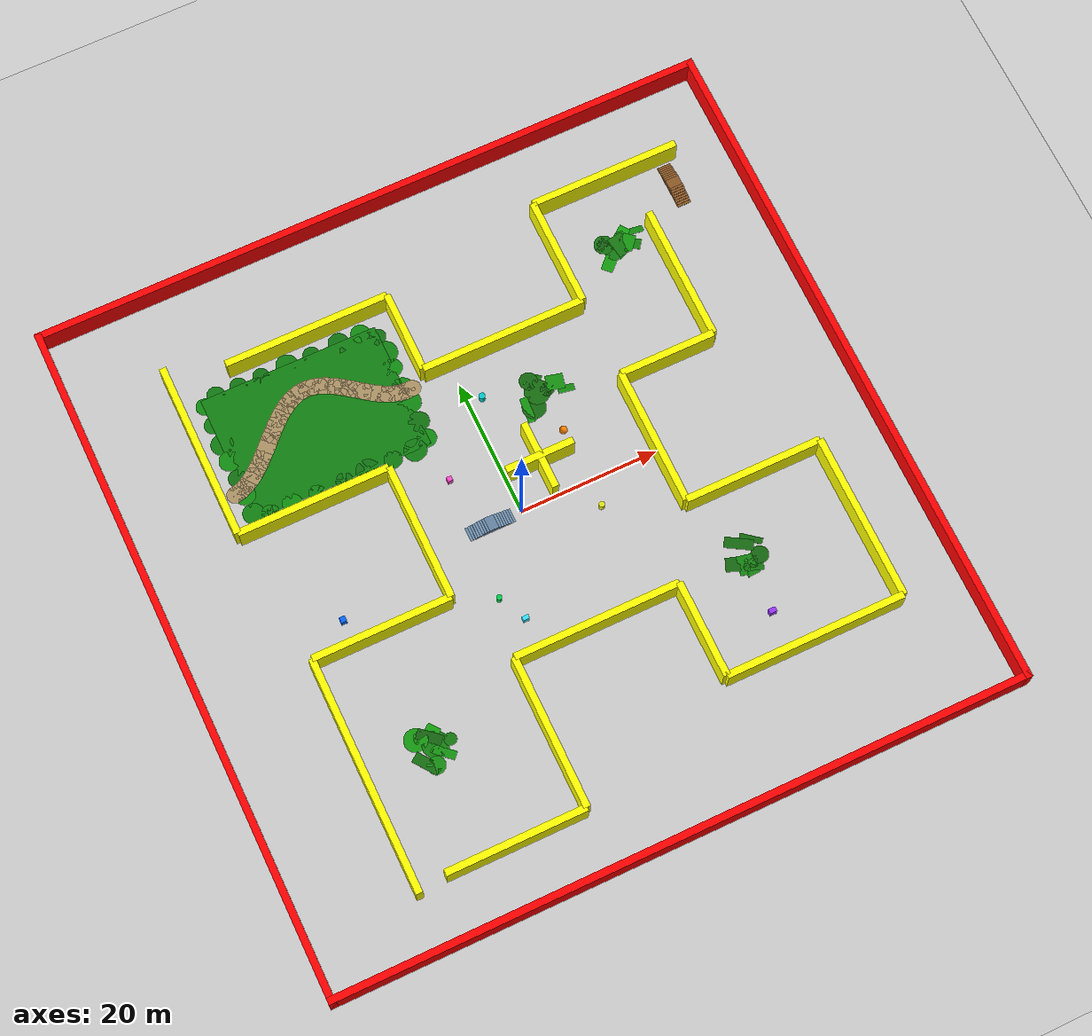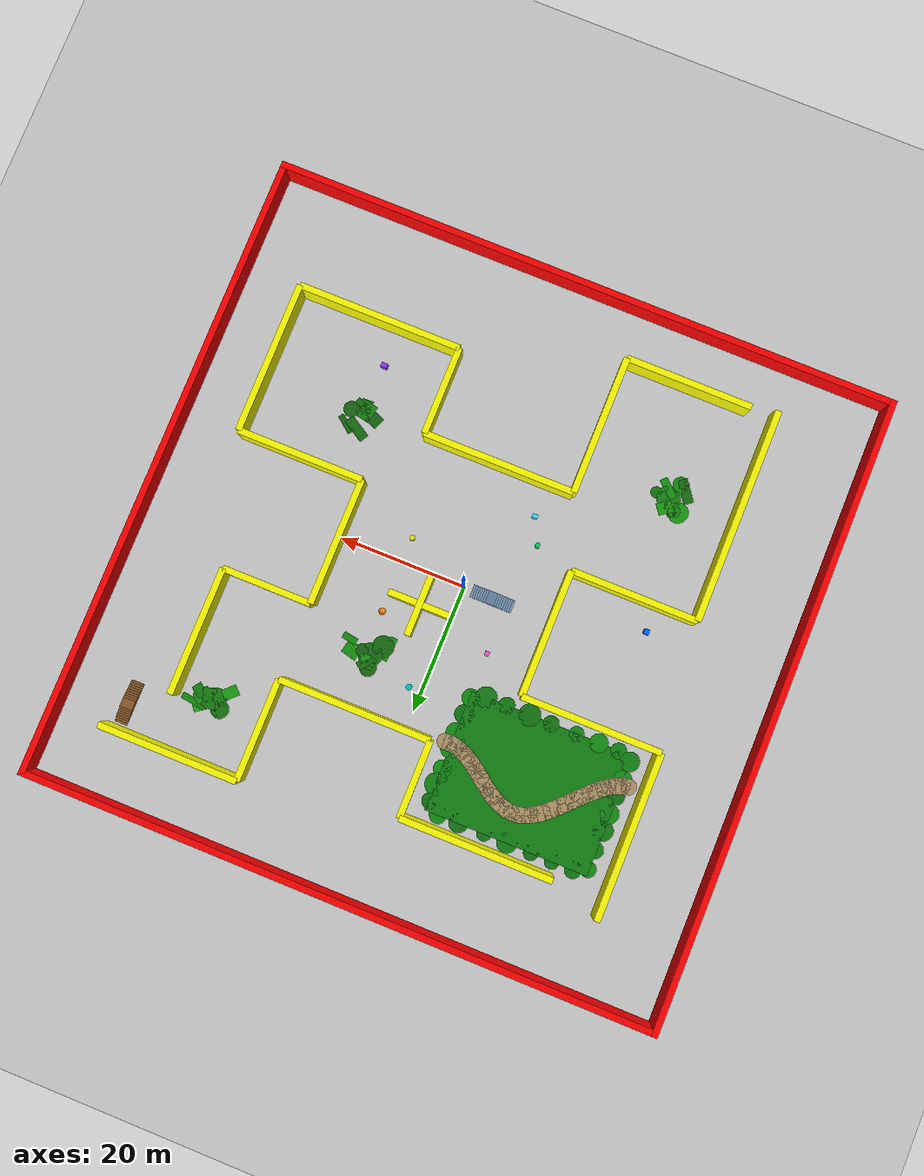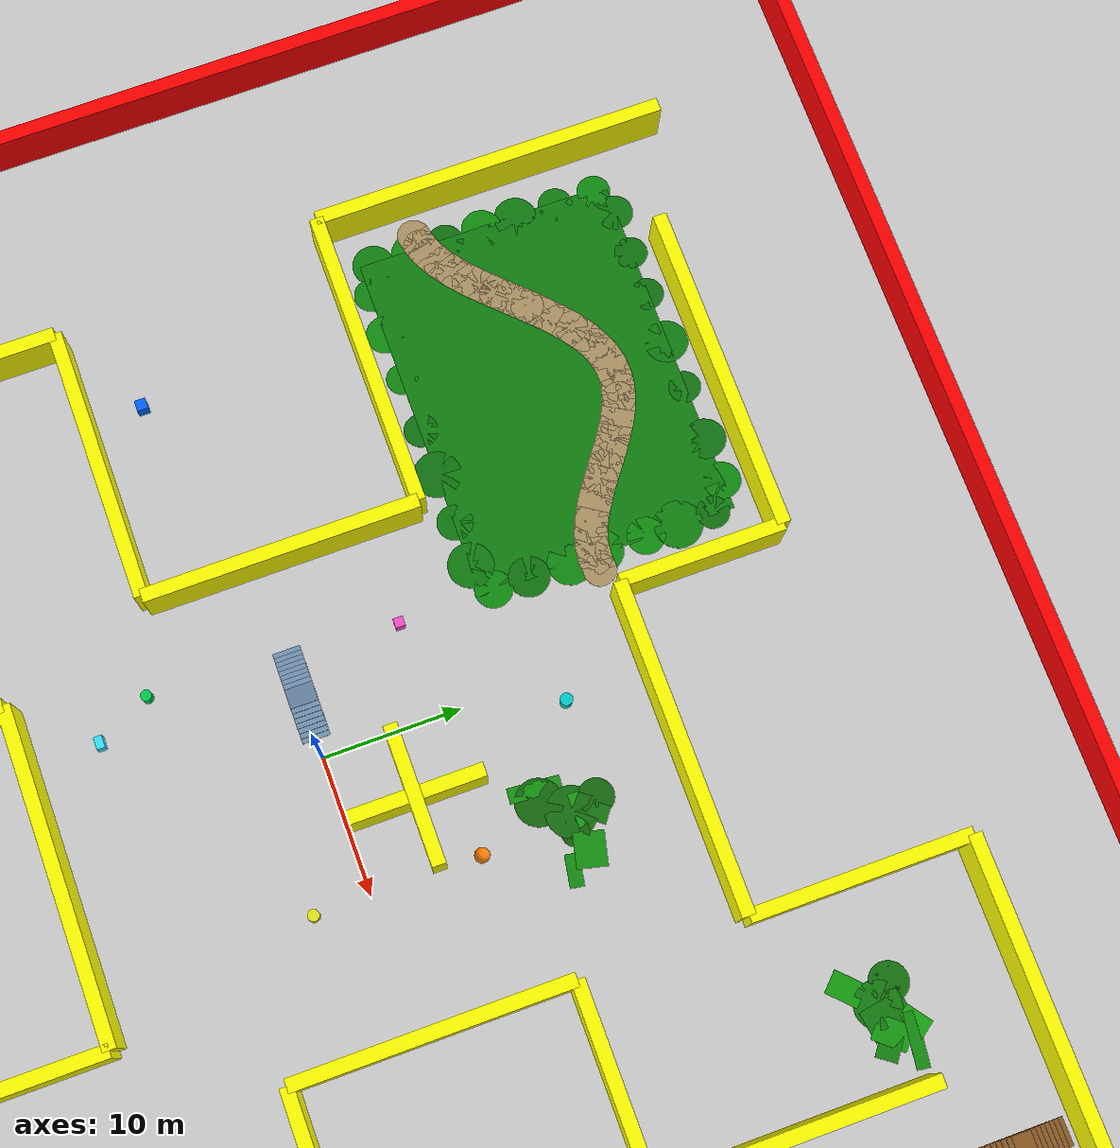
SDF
<sdf version="1.8">
 <world name="semantic_segmentation_world">
  <plugin filename="ignition-gazebo-physics-system" name="ignition::gazebo::systems::Physics"/>
  <plugin filename="ignition-gazebo-user-commands-system" name="ignition::gazebo::systems::UserCommands"/>
  <plugin filename="ignition-gazebo-scene-broadcaster-system" name="ignition::gazebo::systems::SceneBroadcaster"/>
  <plugin filename="ignition-gazebo-sensors-system" name="ignition::gazebo::systems::Sensors">
   <render_engine>ogre2</render_engine>
  </plugin>
  <plugin filename="ignition-gazebo-imu-system" name="ignition::gazebo::systems::Imu"/>
  <physics name="1ms" type="ignored">
   <max_step_size>0.001</max_step_size>
   <real_time_factor>1.0</real_time_factor>
   <gravity>0 0 -9.8</gravity>
  </physics>
  <light type="directional" name="sun">
   <pose>0 0 20 0 0 0</pose>
   <diffuse>0.8 0.8 0.8 1</diffuse>
   <specular>0.2 0.2 0.2 1</specular>
   <attenuation>
    <range>1000</range>
    <constant>0.9</constant>
    <linear>0.01</linear>
    <quadratic>0.001</quadratic>
   </attenuation>
   <direction>-0.5 0.1 -0.9</direction>
  </light>
  <model name="ground_plane">
   <static>true</static>
   <link name="link">
    <collision name="collision">
     <geometry><plane><normal>0 0 1</normal><size>120 120</size></plane></geometry>
     <surface><friction><ode><mu>100</mu><mu2>50</mu2></ode></friction></surface>
    </collision>
    <visual name="visual">
     <geometry><plane><normal>0 0 1</normal><size>100 100</size></plane></geometry>
     <material>
      <ambient>0.8 0.8 0.8 1</ambient>
      <diffuse>0.8 0.8 0.8 1</diffuse>
      <specular>0.8 0.8 0.8 1</specular>
     </material>
    </visual>
   </link>
  </model>
  <model name="outer_boundary">
   <static>true</static>
   <link name="walls">
    <collision name="north_collision">
     <pose>0 49.5 2 0 0 0</pose>
     <geometry><box><size>100 1 4</size></box></geometry>
    </collision>
    <visual name="north_visual">
     <pose>0 49.5 2 0 0 0</pose>
     <geometry><box><size>100 1 4</size></box></geometry>
     <material><ambient>1 0 0 1</ambient><diffuse>1 0 0 1</diffuse></material>
    </visual>
    <collision name="south_collision">
     <pose>0 -49.5 2 0 0 0</pose>
     <geometry><box><size>100 1 4</size></box></geometry>
    </collision>
    <visual name="south_visual">
     <pose>0 -49.5 2 0 0 0</pose>
     <geometry><box><size>100 1 4</size></box></geometry>
     <material><ambient>1 0 0 1</ambient><diffuse>1 0 0 1</diffuse></material>
    </visual>
    <collision name="east_collision">
     <pose>49.5 0 2 0 0 0</pose>
     <geometry><box><size>1 100 4</size></box></geometry>
    </collision>
    <visual name="east_visual">
     <pose>49.5 0 2 0 0 0</pose>
     <geometry><box><size>1 100 4</size></box></geometry>
     <material><ambient>1 0 0 1</ambient><diffuse>1 0 0 1</diffuse></material>
    </visual>
    <collision name="west_collision">
     <pose>-49.5 0 2 0 0 0</pose>
     <geometry><box><size>1 100 4</size></box></geometry>
    </collision>
    <visual name="west_visual">
     <pose>-49.5 0 2 0 0 0</pose>
     <geometry><box><size>1 100 4</size></box></geometry>
     <material><ambient>1 0 0 1</ambient><diffuse>1 0 0 1</diffuse></material>
    </visual>
   </link>
   <plugin filename="ignition-gazebo-label-system" name="ignition::gazebo::systems::Label">
    <label>4</label>
   </plugin>
  </model>
  <model name="large_bent_maze">
   <static>true</static>
   <link name="maze_walls">
    <collision name="m01c">
     <pose>-34 -25 2 0 0 0</pose>
     <geometry><box><size>1 34 4</size></box></geometry>
    </collision>
    <visual name="m01v">
     <pose>-34 -25 2 0 0 0</pose>
     <geometry><box><size>1 34 4</size></box></geometry>
     <material><ambient>1 1 0 1</ambient><diffuse>1 1 0 1</diffuse></material>
    </visual>
    <collision name="m02c">
     <pose>-24 -8 2 0 0 0</pose>
     <geometry><box><size>20 1 4</size></box></geometry>
    </collision>
    <visual name="m02v">
     <pose>-24 -8 2 0 0 0</pose>
     <geometry><box><size>20 1 4</size></box></geometry>
     <material><ambient>1 1 0 1</ambient><diffuse>1 1 0 1</diffuse></material>
    </visual>
    <collision name="m03c">
     <pose>-14 2 2 0 0 0</pose>
     <geometry><box><size>1 20 4</size></box></geometry>
    </collision>
    <visual name="m03v">
     <pose>-14 2 2 0 0 0</pose>
     <geometry><box><size>1 20 4</size></box></geometry>
     <material><ambient>1 1 0 1</ambient><diffuse>1 1 0 1</diffuse></material>
    </visual>
    <collision name="m04c">
     <pose>-25 12 2 0 0 0</pose>
     <geometry><box><size>22 1 4</size></box></geometry>
    </collision>
    <visual name="m04v">
     <pose>-25 12 2 0 0 0</pose>
     <geometry><box><size>22 1 4</size></box></geometry>
     <material><ambient>1 1 0 1</ambient><diffuse>1 1 0 1</diffuse></material>
    </visual>
    <collision name="m05c">
     <pose>-36 25 2 0 0 0</pose>
     <geometry><box><size>1 26 4</size></box></geometry>
    </collision>
    <visual name="m05v">
     <pose>-36 25 2 0 0 0</pose>
     <geometry><box><size>1 26 4</size></box></geometry>
     <material><ambient>1 1 0 1</ambient><diffuse>1 1 0 1</diffuse></material>
    </visual>
    <collision name="m06c">
     <pose>-16 35 2 0 0 0</pose>
     <geometry><box><size>24 1 4</size></box></geometry>
    </collision>
    <visual name="m06v">
     <pose>-16 35 2 0 0 0</pose>
     <geometry><box><size>24 1 4</size></box></geometry>
     <material><ambient>1 1 0 1</ambient><diffuse>1 1 0 1</diffuse></material>
    </visual>
    <collision name="m07c">
     <pose>-4 29 2 0 0 0</pose>
     <geometry><box><size>1 12 4</size></box></geometry>
    </collision>
    <visual name="m07v">
     <pose>-4 29 2 0 0 0</pose>
     <geometry><box><size>1 12 4</size></box></geometry>
     <material><ambient>1 1 0 1</ambient><diffuse>1 1 0 1</diffuse></material>
    </visual>
    <collision name="m08c">
     <pose>8 23 2 0 0 0</pose>
     <geometry><box><size>24 1 4</size></box></geometry>
    </collision>
    <visual name="m08v">
     <pose>8 23 2 0 0 0</pose>
     <geometry><box><size>24 1 4</size></box></geometry>
     <material><ambient>1 1 0 1</ambient><diffuse>1 1 0 1</diffuse></material>
    </visual>
    <collision name="m09c">
     <pose>20 31 2 0 0 0</pose>
     <geometry><box><size>1 16 4</size></box></geometry>
    </collision>
    <visual name="m09v">
     <pose>20 31 2 0 0 0</pose>
     <geometry><box><size>1 16 4</size></box></geometry>
     <material><ambient>1 1 0 1</ambient><diffuse>1 1 0 1</diffuse></material>
    </visual>
    <collision name="m10c">
     <pose>31 39 2 0 0 0</pose>
     <geometry><box><size>22 1 4</size></box></geometry>
    </collision>
    <visual name="m10v">
     <pose>31 39 2 0 0 0</pose>
     <geometry><box><size>22 1 4</size></box></geometry>
     <material><ambient>1 1 0 1</ambient><diffuse>1 1 0 1</diffuse></material>
    </visual>
    <collision name="m11c">
     <pose>34 21 2 0 0 0</pose>
     <geometry><box><size>1 20 4</size></box></geometry>
    </collision>
    <visual name="m11v">
     <pose>34 21 2 0 0 0</pose>
     <geometry><box><size>1 20 4</size></box></geometry>
     <material><ambient>1 1 0 1</ambient><diffuse>1 1 0 1</diffuse></material>
    </visual>
    <collision name="m12c">
     <pose>27 11 2 0 0 0</pose>
     <geometry><box><size>14 1 4</size></box></geometry>
    </collision>
    <visual name="m12v">
     <pose>27 11 2 0 0 0</pose>
     <geometry><box><size>14 1 4</size></box></geometry>
     <material><ambient>1 1 0 1</ambient><diffuse>1 1 0 1</diffuse></material>
    </visual>
    <collision name="m13c">
     <pose>20 1 2 0 0 0</pose>
     <geometry><box><size>1 20 4</size></box></geometry>
    </collision>
    <visual name="m13v">
     <pose>20 1 2 0 0 0</pose>
     <geometry><box><size>1 20 4</size></box></geometry>
     <material><ambient>1 1 0 1</ambient><diffuse>1 1 0 1</diffuse></material>
    </visual>
    <collision name="m14c">
     <pose>30 -9 2 0 0 0</pose>
     <geometry><box><size>20 1 4</size></box></geometry>
    </collision>
    <visual name="m14v">
     <pose>30 -9 2 0 0 0</pose>
     <geometry><box><size>20 1 4</size></box></geometry>
     <material><ambient>1 1 0 1</ambient><diffuse>1 1 0 1</diffuse></material>
    </visual>
    <collision name="m15c">
     <pose>40 -21 2 0 0 0</pose>
     <geometry><box><size>1 24 4</size></box></geometry>
    </collision>
    <visual name="m15v">
     <pose>40 -21 2 0 0 0</pose>
     <geometry><box><size>1 24 4</size></box></geometry>
     <material><ambient>1 1 0 1</ambient><diffuse>1 1 0 1</diffuse></material>
    </visual>
    <collision name="m16c">
     <pose>27 -33 2 0 0 0</pose>
     <geometry><box><size>26 1 4</size></box></geometry>
    </collision>
    <visual name="m16v">
     <pose>27 -33 2 0 0 0</pose>
     <geometry><box><size>26 1 4</size></box></geometry>
     <material><ambient>1 1 0 1</ambient><diffuse>1 1 0 1</diffuse></material>
    </visual>
    <collision name="m17c">
     <pose>14 -26 2 0 0 0</pose>
     <geometry><box><size>1 14 4</size></box></geometry>
    </collision>
    <visual name="m17v">
     <pose>14 -26 2 0 0 0</pose>
     <geometry><box><size>1 14 4</size></box></geometry>
     <material><ambient>1 1 0 1</ambient><diffuse>1 1 0 1</diffuse></material>
    </visual>
    <collision name="m18c">
     <pose>2 -19 2 0 0 0</pose>
     <geometry><box><size>24 1 4</size></box></geometry>
    </collision>
    <visual name="m18v">
     <pose>2 -19 2 0 0 0</pose>
     <geometry><box><size>24 1 4</size></box></geometry>
     <material><ambient>1 1 0 1</ambient><diffuse>1 1 0 1</diffuse></material>
    </visual>
    <collision name="m19c">
     <pose>-10 -30 2 0 0 0</pose>
     <geometry><box><size>1 22 4</size></box></geometry>
    </collision>
    <visual name="m19v">
     <pose>-10 -30 2 0 0 0</pose>
     <geometry><box><size>1 22 4</size></box></geometry>
     <material><ambient>1 1 0 1</ambient><diffuse>1 1 0 1</diffuse></material>
    </visual>
    <collision name="m20c">
     <pose>-20 -41 2 0 0 0</pose>
     <geometry><box><size>20 1 4</size></box></geometry>
    </collision>
    <visual name="m20v">
     <pose>-20 -41 2 0 0 0</pose>
     <geometry><box><size>20 1 4</size></box></geometry>
     <material><ambient>1 1 0 1</ambient><diffuse>1 1 0 1</diffuse></material>
    </visual>
    <collision name="m21c"><pose>5 5 2 0 0 0</pose><geometry><box><size>10 1 4</size></box></geometry></collision>
    <visual name="m21v">
     <pose>5 5 2 0 0 0</pose>
     <geometry><box><size>10 1 4</size></box></geometry>
     <material><ambient>1 1 0 1</ambient><diffuse>1 1 0 1</diffuse></material>
    </visual>
    <collision name="m22c"><pose>5 5 2 0 0 0</pose><geometry><box><size>1 10 4</size></box></geometry></collision>
    <visual name="m22v">
     <pose>5 5 2 0 0 0</pose>
     <geometry><box><size>1 10 4</size></box></geometry>
     <material><ambient>1 1 0 1</ambient><diffuse>1 1 0 1</diffuse></material>
    </visual>
   </link>
   <plugin filename="ignition-gazebo-label-system" name="ignition::gazebo::systems::Label">
    <label>5</label>
   </plugin>
  </model>
  <model name="dynamic_obstacle_1">
   <static>true</static>
   <pose>-28 -4 0.6 0 0 0</pose>
   <link name="body">
    <inertial><mass>1</mass><inertia><ixx>0.12</ixx><iyy>0.12</iyy><izz>0.12</izz></inertia></inertial>
    <velocity_decay><linear>0.4</linear><angular>0.8</angular></velocity_decay>
    <collision name="collision">
     <geometry><box><size>0.8 0.8 1.2</size></box></geometry>
     <surface><friction><ode><mu>0.2</mu><mu2>0.2</mu2></ode></friction></surface>
    </collision>
    <visual name="visual">
     <geometry><box><size>0.8 0.8 1.2</size></box></geometry>
     <material><ambient>0 0.4 1 1</ambient><diffuse>0 0.4 1 1</diffuse></material>
    </visual>
   </link>
   <plugin filename="ignition-gazebo-label-system" name="ignition::gazebo::systems::Label">
    <label>6</label>
   </plugin>
   <plugin filename="libssmi_periodic_motion_system.so" name="semantic_segmentation_husky::PeriodicMotionSystem">
    <offset>10 0 0</offset>
    <period>30</period>
    <phase>7.5</phase>
   </plugin>
  </model>
  <model name="dynamic_obstacle_2">
   <static>true</static>
   <pose>2 17 0.6 0 0 0</pose>
   <link name="body">
    <inertial><mass>1</mass><inertia><ixx>0.12</ixx><iyy>0.12</iyy><izz>0.12</izz></inertia></inertial>
    <velocity_decay><linear>0.4</linear><angular>0.8</angular></velocity_decay>
    <collision name="collision">
     <geometry><cylinder><radius>0.45</radius><length>1.2</length></cylinder></geometry>
     <surface><friction><ode><mu>0.2</mu><mu2>0.2</mu2></ode></friction></surface>
    </collision>
    <visual name="visual">
     <geometry><cylinder><radius>0.45</radius><length>1.2</length></cylinder></geometry>
     <material><ambient>0 0.8 0.8 1</ambient><diffuse>0 0.8 0.8 1</diffuse></material>
    </visual>
   </link>
   <plugin filename="ignition-gazebo-label-system" name="ignition::gazebo::systems::Label">
    <label>6</label>
   </plugin>
   <plugin filename="libssmi_periodic_motion_system.so" name="semantic_segmentation_husky::PeriodicMotionSystem">
    <offset>14 0 0</offset>
    <period>42</period>
    <phase>10.5</phase>
   </plugin>
  </model>
  <model name="dynamic_obstacle_3">
   <static>true</static>
   <pose>24 -27 0.6 0 0 0</pose>
   <link name="body">
    <inertial><mass>1</mass><inertia><ixx>0.12</ixx><iyy>0.12</iyy><izz>0.12</izz></inertia></inertial>
    <velocity_decay><linear>0.4</linear><angular>0.8</angular></velocity_decay>
    <collision name="collision">
     <geometry><box><size>1.0 0.7 1.2</size></box></geometry>
     <surface><friction><ode><mu>0.2</mu><mu2>0.2</mu2></ode></friction></surface>
    </collision>
    <visual name="visual">
     <geometry><box><size>1.0 0.7 1.2</size></box></geometry>
     <material><ambient>0.6 0.2 1 1</ambient><diffuse>0.6 0.2 1 1</diffuse></material>
    </visual>
   </link>
   <plugin filename="ignition-gazebo-label-system" name="ignition::gazebo::systems::Label">
    <label>6</label>
   </plugin>
   <plugin filename="libssmi_periodic_motion_system.so" name="semantic_segmentation_husky::PeriodicMotionSystem">
    <offset>10 10 0</offset>
    <period>45</period>
    <phase>11.25</phase>
   </plugin>
  </model>
  <model name="dynamic_obstacle_4">
   <static>true</static>
   <pose>-8 -10 0.55 0 0 0</pose>
   <link name="body">
    <inertial><mass>1</mass><inertia><ixx>0.1</ixx><iyy>0.1</iyy><izz>0.1</izz></inertia></inertial>
    <velocity_decay><linear>0.4</linear><angular>0.8</angular></velocity_decay>
    <collision name="collision">
     <geometry><cylinder><radius>0.4</radius><length>1.1</length></cylinder></geometry>
     <surface><friction><ode><mu>0.2</mu><mu2>0.2</mu2></ode></friction></surface>
    </collision>
    <visual name="visual">
     <geometry><cylinder><radius>0.4</radius><length>1.1</length></cylinder></geometry>
     <material><ambient>0 0.8 0.3 1</ambient><diffuse>0 0.8 0.3 1</diffuse></material>
    </visual>
   </link>
   <plugin filename="ignition-gazebo-label-system" name="ignition::gazebo::systems::Label">
    <label>6</label>
   </plugin>
   <plugin filename="libssmi_periodic_motion_system.so" name="semantic_segmentation_husky::PeriodicMotionSystem">
    <offset>16 0 0</offset>
    <period>48</period>
    <phase>12</phase>
   </plugin>
  </model>
  <model name="dynamic_obstacle_5">
   <static>true</static>
   <pose>-7 8 0.55 0 0 1.5708</pose>
   <link name="body">
    <inertial><mass>1</mass><inertia><ixx>0.1</ixx><iyy>0.1</iyy><izz>0.1</izz></inertia></inertial>
    <velocity_decay><linear>0.4</linear><angular>0.8</angular></velocity_decay>
    <collision name="collision">
     <geometry><box><size>0.7 0.7 1.1</size></box></geometry>
     <surface><friction><ode><mu>0.2</mu><mu2>0.2</mu2></ode></friction></surface>
    </collision>
    <visual name="visual">
     <geometry><box><size>0.7 0.7 1.1</size></box></geometry>
     <material><ambient>1 0.3 0.8 1</ambient><diffuse>1 0.3 0.8 1</diffuse></material>
    </visual>
   </link>
   <plugin filename="ignition-gazebo-label-system" name="ignition::gazebo::systems::Label">
    <label>6</label>
   </plugin>
   <plugin filename="libssmi_periodic_motion_system.so" name="semantic_segmentation_husky::PeriodicMotionSystem">
    <offset>0 12 0</offset>
    <period>36</period>
    <phase>9</phase>
   </plugin>
  </model>
  <model name="dynamic_obstacle_6">
   <static>true</static>
   <pose>10 8 0.55 0 0 0</pose>
   <link name="body">
    <inertial><mass>1</mass><inertia><ixx>0.1</ixx><iyy>0.1</iyy><izz>0.1</izz></inertia></inertial>
    <velocity_decay><linear>0.4</linear><angular>0.8</angular></velocity_decay>
    <collision name="collision">
     <geometry><sphere><radius>0.55</radius></sphere></geometry>
     <surface><friction><ode><mu>0.2</mu><mu2>0.2</mu2></ode></friction></surface>
    </collision>
    <visual name="visual">
     <geometry><sphere><radius>0.55</radius></sphere></geometry>
     <material><ambient>1 0.5 0 1</ambient><diffuse>1 0.5 0 1</diffuse></material>
    </visual>
   </link>
   <plugin filename="ignition-gazebo-label-system" name="ignition::gazebo::systems::Label">
    <label>6</label>
   </plugin>
   <plugin filename="libssmi_periodic_motion_system.so" name="semantic_segmentation_husky::PeriodicMotionSystem">
    <offset>7 0 0</offset>
    <period>22</period>
    <phase>5.5</phase>
   </plugin>
  </model>
  <model name="dynamic_obstacle_7">
   <static>true</static>
   <pose>-6 -14 0.55 0 0 0</pose>
   <link name="body">
    <inertial><mass>1</mass><inertia><ixx>0.1</ixx><iyy>0.1</iyy><izz>0.1</izz></inertia></inertial>
    <velocity_decay><linear>0.4</linear><angular>0.8</angular></velocity_decay>
    <collision name="collision">
     <geometry><box><size>0.9 0.6 1.1</size></box></geometry>
     <surface><friction><ode><mu>0.2</mu><mu2>0.2</mu2></ode></friction></surface>
    </collision>
    <visual name="visual">
     <geometry><box><size>0.9 0.6 1.1</size></box></geometry>
     <material><ambient>0.2 0.9 1 1</ambient><diffuse>0.2 0.9 1 1</diffuse></material>
    </visual>
   </link>
   <plugin filename="ignition-gazebo-label-system" name="ignition::gazebo::systems::Label">
    <label>5</label>
   </plugin>
   <plugin filename="libssmi_periodic_motion_system.so" name="semantic_segmentation_husky::PeriodicMotionSystem">
    <offset>14 0 0</offset>
    <period>42</period>
    <phase>10.5</phase>
   </plugin>
  </model>
  <model name="dynamic_obstacle_8">
   <static>true</static>
   <pose>10 -4 0.55 0 0 -1.5708</pose>
   <link name="body">
    <inertial><mass>1</mass><inertia><ixx>0.1</ixx><iyy>0.1</iyy><izz>0.1</izz></inertia></inertial>
    <velocity_decay><linear>0.4</linear><angular>0.8</angular></velocity_decay>
    <collision name="collision">
     <geometry><cylinder><radius>0.42</radius><length>1.1</length></cylinder></geometry>
     <surface><friction><ode><mu>0.2</mu><mu2>0.2</mu2></ode></friction></surface>
    </collision>
    <visual name="visual">
     <geometry><cylinder><radius>0.42</radius><length>1.1</length></cylinder></geometry>
     <material><ambient>0.9 0.9 0.1 1</ambient><diffuse>0.9 0.9 0.1 1</diffuse></material>
    </visual>
   </link>
   <plugin filename="ignition-gazebo-label-system" name="ignition::gazebo::systems::Label">
    <label>5</label>
   </plugin>
   <plugin filename="libssmi_periodic_motion_system.so" name="semantic_segmentation_husky::PeriodicMotionSystem">
    <offset>0 -12 0</offset>
    <period>36</period>
    <phase>9</phase>
   </plugin>
  </model>
  <model name="staircase">
   <static>true</static>
   <pose>-8 0 0 0 0 0</pose>
   <link name="stairs">
    <collision name="step_1_collision">
     <pose>0.175 0 0.05 0 0 0</pose>
     <geometry><box><size>0.35 2.0 0.10</size></box></geometry>
     <surface><friction><ode><mu>1.0</mu><mu2>1.0</mu2></ode></friction></surface>
    </collision>
    <visual name="step_1_visual">
     <pose>0.175 0 0.05 0 0 0</pose>
     <geometry><box><size>0.35 2.0 0.10</size></box></geometry>
     <material><ambient>0.35 0.45 0.55 1</ambient><diffuse>0.45 0.58 0.70 1</diffuse></material>
    </visual>
    <collision name="step_2_collision">
     <pose>0.525 0 0.10 0 0 0</pose>
     <geometry><box><size>0.35 2.0 0.20</size></box></geometry>
     <surface><friction><ode><mu>1.0</mu><mu2>1.0</mu2></ode></friction></surface>
    </collision>
    <visual name="step_2_visual">
     <pose>0.525 0 0.10 0 0 0</pose>
     <geometry><box><size>0.35 2.0 0.20</size></box></geometry>
     <material><ambient>0.35 0.45 0.55 1</ambient><diffuse>0.45 0.58 0.70 1</diffuse></material>
    </visual>
    <collision name="step_3_collision">
     <pose>0.875 0 0.15 0 0 0</pose>
     <geometry><box><size>0.35 2.0 0.30</size></box></geometry>
     <surface><friction><ode><mu>1.0</mu><mu2>1.0</mu2></ode></friction></surface>
    </collision>
    <visual name="step_3_visual">
     <pose>0.875 0 0.15 0 0 0</pose>
     <geometry><box><size>0.35 2.0 0.30</size></box></geometry>
     <material><ambient>0.35 0.45 0.55 1</ambient><diffuse>0.45 0.58 0.70 1</diffuse></material>
    </visual>
    <collision name="step_4_collision">
     <pose>1.225 0 0.20 0 0 0</pose>
     <geometry><box><size>0.35 2.0 0.40</size></box></geometry>
     <surface><friction><ode><mu>1.0</mu><mu2>1.0</mu2></ode></friction></surface>
    </collision>
    <visual name="step_4_visual">
     <pose>1.225 0 0.20 0 0 0</pose>
     <geometry><box><size>0.35 2.0 0.40</size></box></geometry>
     <material><ambient>0.35 0.45 0.55 1</ambient><diffuse>0.45 0.58 0.70 1</diffuse></material>
    </visual>
    <collision name="step_5_collision">
     <pose>1.575 0 0.25 0 0 0</pose>
     <geometry><box><size>0.35 2.0 0.50</size></box></geometry>
     <surface><friction><ode><mu>1.0</mu><mu2>1.0</mu2></ode></friction></surface>
    </collision>
    <visual name="step_5_visual">
     <pose>1.575 0 0.25 0 0 0</pose>
     <geometry><box><size>0.35 2.0 0.50</size></box></geometry>
     <material><ambient>0.35 0.45 0.55 1</ambient><diffuse>0.45 0.58 0.70 1</diffuse></material>
    </visual>
    <collision name="step_6_collision">
     <pose>1.925 0 0.30 0 0 0</pose>
     <geometry><box><size>0.35 2.0 0.60</size></box></geometry>
     <surface><friction><ode><mu>1.0</mu><mu2>1.0</mu2></ode></friction></surface>
    </collision>
    <visual name="step_6_visual">
     <pose>1.925 0 0.30 0 0 0</pose>
     <geometry><box><size>0.35 2.0 0.60</size></box></geometry>
     <material><ambient>0.35 0.45 0.55 1</ambient><diffuse>0.45 0.58 0.70 1</diffuse></material>
    </visual>
    <collision name="step_7_collision">
     <pose>2.275 0 0.35 0 0 0</pose>
     <geometry><box><size>0.35 2.0 0.70</size></box></geometry>
     <surface><friction><ode><mu>1.0</mu><mu2>1.0</mu2></ode></friction></surface>
    </collision>
    <visual name="step_7_visual">
     <pose>2.275 0 0.35 0 0 0</pose>
     <geometry><box><size>0.35 2.0 0.70</size></box></geometry>
     <material><ambient>0.35 0.45 0.55 1</ambient><diffuse>0.45 0.58 0.70 1</diffuse></material>
    </visual>
    <collision name="step_8_collision">
     <pose>2.625 0 0.40 0 0 0</pose>
     <geometry><box><size>0.35 2.0 0.80</size></box></geometry>
     <surface><friction><ode><mu>1.0</mu><mu2>1.0</mu2></ode></friction></surface>
    </collision>
    <visual name="step_8_visual">
     <pose>2.625 0 0.40 0 0 0</pose>
     <geometry><box><size>0.35 2.0 0.80</size></box></geometry>
     <material><ambient>0.35 0.45 0.55 1</ambient><diffuse>0.45 0.58 0.70 1</diffuse></material>
    </visual>
    <collision name="top_platform_collision">
     <pose>3.50 0 0.40 0 0 0</pose>
     <geometry><box><size>1.40 2.0 0.80</size></box></geometry>
     <surface><friction><ode><mu>1.0</mu><mu2>1.0</mu2></ode></friction></surface>
    </collision>
    <visual name="top_platform_visual">
     <pose>3.50 0 0.40 0 0 0</pose>
     <geometry><box><size>1.40 2.0 0.80</size></box></geometry>
     <material><ambient>0.30 0.40 0.50 1</ambient><diffuse>0.40 0.52 0.64 1</diffuse></material>
    </visual>
    <collision name="down_step_1_collision">
     <pose>4.375 0 0.35 0 0 0</pose>
     <geometry><box><size>0.35 2.0 0.70</size></box></geometry>
     <surface><friction><ode><mu>1.0</mu><mu2>1.0</mu2></ode></friction></surface>
    </collision>
    <visual name="down_step_1_visual">
     <pose>4.375 0 0.35 0 0 0</pose>
     <geometry><box><size>0.35 2.0 0.70</size></box></geometry>
     <material><ambient>0.35 0.45 0.55 1</ambient><diffuse>0.45 0.58 0.70 1</diffuse></material>
    </visual>
    <collision name="down_step_2_collision">
     <pose>4.725 0 0.30 0 0 0</pose>
     <geometry><box><size>0.35 2.0 0.60</size></box></geometry>
     <surface><friction><ode><mu>1.0</mu><mu2>1.0</mu2></ode></friction></surface>
    </collision>
    <visual name="down_step_2_visual">
     <pose>4.725 0 0.30 0 0 0</pose>
     <geometry><box><size>0.35 2.0 0.60</size></box></geometry>
     <material><ambient>0.35 0.45 0.55 1</ambient><diffuse>0.45 0.58 0.70 1</diffuse></material>
    </visual>
    <collision name="down_step_3_collision">
     <pose>5.075 0 0.25 0 0 0</pose>
     <geometry><box><size>0.35 2.0 0.50</size></box></geometry>
     <surface><friction><ode><mu>1.0</mu><mu2>1.0</mu2></ode></friction></surface>
    </collision>
    <visual name="down_step_3_visual">
     <pose>5.075 0 0.25 0 0 0</pose>
     <geometry><box><size>0.35 2.0 0.50</size></box></geometry>
     <material><ambient>0.35 0.45 0.55 1</ambient><diffuse>0.45 0.58 0.70 1</diffuse></material>
    </visual>
    <collision name="down_step_4_collision">
     <pose>5.425 0 0.20 0 0 0</pose>
     <geometry><box><size>0.35 2.0 0.40</size></box></geometry>
     <surface><friction><ode><mu>1.0</mu><mu2>1.0</mu2></ode></friction></surface>
    </collision>
    <visual name="down_step_4_visual">
     <pose>5.425 0 0.20 0 0 0</pose>
     <geometry><box><size>0.35 2.0 0.40</size></box></geometry>
     <material><ambient>0.35 0.45 0.55 1</ambient><diffuse>0.45 0.58 0.70 1</diffuse></material>
    </visual>
    <collision name="down_step_5_collision">
     <pose>5.775 0 0.15 0 0 0</pose>
     <geometry><box><size>0.35 2.0 0.30</size></box></geometry>
     <surface><friction><ode><mu>1.0</mu><mu2>1.0</mu2></ode></friction></surface>
    </collision>
    <visual name="down_step_5_visual">
     <pose>5.775 0 0.15 0 0 0</pose>
     <geometry><box><size>0.35 2.0 0.30</size></box></geometry>
     <material><ambient>0.35 0.45 0.55 1</ambient><diffuse>0.45 0.58 0.70 1</diffuse></material>
    </visual>
    <collision name="down_step_6_collision">
     <pose>6.125 0 0.10 0 0 0</pose>
     <geometry><box><size>0.35 2.0 0.20</size></box></geometry>
     <surface><friction><ode><mu>1.0</mu><mu2>1.0</mu2></ode></friction></surface>
    </collision>
    <visual name="down_step_6_visual">
     <pose>6.125 0 0.10 0 0 0</pose>
     <geometry><box><size>0.35 2.0 0.20</size></box></geometry>
     <material><ambient>0.35 0.45 0.55 1</ambient><diffuse>0.45 0.58 0.70 1</diffuse></material>
    </visual>
    <collision name="down_step_7_collision">
     <pose>6.475 0 0.05 0 0 0</pose>
     <geometry><box><size>0.35 2.0 0.10</size></box></geometry>
     <surface><friction><ode><mu>1.0</mu><mu2>1.0</mu2></ode></friction></surface>
    </collision>
    <visual name="down_step_7_visual">
     <pose>6.475 0 0.05 0 0 0</pose>
     <geometry><box><size>0.35 2.0 0.10</size></box></geometry>
     <material><ambient>0.35 0.45 0.55 1</ambient><diffuse>0.45 0.58 0.70 1</diffuse></material>
    </visual>
   </link>
   <plugin filename="ignition-gazebo-label-system" name="ignition::gazebo::systems::Label">
    <label>7</label>
   </plugin>
  </model>
  <model name="staircase_upper_right">
   <static>true</static>
   <pose>40 31.5 0 0 0 1.57079632679</pose>
   <link name="stairs">
    <collision name="up_step_1_collision">
     <pose>0.175 0 0.05 0 0 0</pose>
     <geometry><box><size>0.35 2.0 0.10</size></box></geometry>
     <surface><friction><ode><mu>1.0</mu><mu2>1.0</mu2></ode></friction></surface>
    </collision>
    <visual name="up_step_1_visual">
     <pose>0.175 0 0.05 0 0 0</pose>
     <geometry><box><size>0.35 2.0 0.10</size></box></geometry>
     <material><ambient>0.55 0.35 0.15 1</ambient><diffuse>0.55 0.35 0.15 1</diffuse></material>
    </visual>
    <collision name="up_step_2_collision">
     <pose>0.525 0 0.10 0 0 0</pose>
     <geometry><box><size>0.35 2.0 0.20</size></box></geometry>
     <surface><friction><ode><mu>1.0</mu><mu2>1.0</mu2></ode></friction></surface>
    </collision>
    <visual name="up_step_2_visual">
     <pose>0.525 0 0.10 0 0 0</pose>
     <geometry><box><size>0.35 2.0 0.20</size></box></geometry>
     <material><ambient>0.55 0.35 0.15 1</ambient><diffuse>0.55 0.35 0.15 1</diffuse></material>
    </visual>
    <collision name="up_step_3_collision">
     <pose>0.875 0 0.15 0 0 0</pose>
     <geometry><box><size>0.35 2.0 0.30</size></box></geometry>
     <surface><friction><ode><mu>1.0</mu><mu2>1.0</mu2></ode></friction></surface>
    </collision>
    <visual name="up_step_3_visual">
     <pose>0.875 0 0.15 0 0 0</pose>
     <geometry><box><size>0.35 2.0 0.30</size></box></geometry>
     <material><ambient>0.55 0.35 0.15 1</ambient><diffuse>0.55 0.35 0.15 1</diffuse></material>
    </visual>
    <collision name="up_step_4_collision">
     <pose>1.225 0 0.20 0 0 0</pose>
     <geometry><box><size>0.35 2.0 0.40</size></box></geometry>
     <surface><friction><ode><mu>1.0</mu><mu2>1.0</mu2></ode></friction></surface>
    </collision>
    <visual name="up_step_4_visual">
     <pose>1.225 0 0.20 0 0 0</pose>
     <geometry><box><size>0.35 2.0 0.40</size></box></geometry>
     <material><ambient>0.55 0.35 0.15 1</ambient><diffuse>0.55 0.35 0.15 1</diffuse></material>
    </visual>
    <collision name="up_step_5_collision">
     <pose>1.575 0 0.25 0 0 0</pose>
     <geometry><box><size>0.35 2.0 0.50</size></box></geometry>
     <surface><friction><ode><mu>1.0</mu><mu2>1.0</mu2></ode></friction></surface>
    </collision>
    <visual name="up_step_5_visual">
     <pose>1.575 0 0.25 0 0 0</pose>
     <geometry><box><size>0.35 2.0 0.50</size></box></geometry>
     <material><ambient>0.55 0.35 0.15 1</ambient><diffuse>0.55 0.35 0.15 1</diffuse></material>
    </visual>
    <collision name="up_step_6_collision">
     <pose>1.925 0 0.30 0 0 0</pose>
     <geometry><box><size>0.35 2.0 0.60</size></box></geometry>
     <surface><friction><ode><mu>1.0</mu><mu2>1.0</mu2></ode></friction></surface>
    </collision>
    <visual name="up_step_6_visual">
     <pose>1.925 0 0.30 0 0 0</pose>
     <geometry><box><size>0.35 2.0 0.60</size></box></geometry>
     <material><ambient>0.55 0.35 0.15 1</ambient><diffuse>0.55 0.35 0.15 1</diffuse></material>
    </visual>
    <collision name="up_step_7_collision">
     <pose>2.275 0 0.35 0 0 0</pose>
     <geometry><box><size>0.35 2.0 0.70</size></box></geometry>
     <surface><friction><ode><mu>1.0</mu><mu2>1.0</mu2></ode></friction></surface>
    </collision>
    <visual name="up_step_7_visual">
     <pose>2.275 0 0.35 0 0 0</pose>
     <geometry><box><size>0.35 2.0 0.70</size></box></geometry>
     <material><ambient>0.55 0.35 0.15 1</ambient><diffuse>0.55 0.35 0.15 1</diffuse></material>
    </visual>
    <collision name="up_step_8_collision">
     <pose>2.625 0 0.40 0 0 0</pose>
     <geometry><box><size>0.35 2.0 0.80</size></box></geometry>
     <surface><friction><ode><mu>1.0</mu><mu2>1.0</mu2></ode></friction></surface>
    </collision>
    <visual name="up_step_8_visual">
     <pose>2.625 0 0.40 0 0 0</pose>
     <geometry><box><size>0.35 2.0 0.80</size></box></geometry>
     <material><ambient>0.55 0.35 0.15 1</ambient><diffuse>0.55 0.35 0.15 1</diffuse></material>
    </visual>
    <collision name="top_platform_collision">
     <pose>3.50 0 0.40 0 0 0</pose>
     <geometry><box><size>1.40 2.0 0.80</size></box></geometry>
     <surface><friction><ode><mu>1.0</mu><mu2>1.0</mu2></ode></friction></surface>
    </collision>
    <visual name="top_platform_visual">
     <pose>3.50 0 0.40 0 0 0</pose>
     <geometry><box><size>1.40 2.0 0.80</size></box></geometry>
     <material><ambient>0.55 0.35 0.15 1</ambient><diffuse>0.55 0.35 0.15 1</diffuse></material>
    </visual>
    <collision name="down_step_1_collision">
     <pose>4.375 0 0.35 0 0 0</pose>
     <geometry><box><size>0.35 2.0 0.70</size></box></geometry>
     <surface><friction><ode><mu>1.0</mu><mu2>1.0</mu2></ode></friction></surface>
    </collision>
    <visual name="down_step_1_visual">
     <pose>4.375 0 0.35 0 0 0</pose>
     <geometry><box><size>0.35 2.0 0.70</size></box></geometry>
     <material><ambient>0.55 0.35 0.15 1</ambient><diffuse>0.55 0.35 0.15 1</diffuse></material>
    </visual>
    <collision name="down_step_2_collision">
     <pose>4.725 0 0.30 0 0 0</pose>
     <geometry><box><size>0.35 2.0 0.60</size></box></geometry>
     <surface><friction><ode><mu>1.0</mu><mu2>1.0</mu2></ode></friction></surface>
    </collision>
    <visual name="down_step_2_visual">
     <pose>4.725 0 0.30 0 0 0</pose>
     <geometry><box><size>0.35 2.0 0.60</size></box></geometry>
     <material><ambient>0.55 0.35 0.15 1</ambient><diffuse>0.55 0.35 0.15 1</diffuse></material>
    </visual>
    <collision name="down_step_3_collision">
     <pose>5.075 0 0.25 0 0 0</pose>
     <geometry><box><size>0.35 2.0 0.50</size></box></geometry>
     <surface><friction><ode><mu>1.0</mu><mu2>1.0</mu2></ode></friction></surface>
    </collision>
    <visual name="down_step_3_visual">
     <pose>5.075 0 0.25 0 0 0</pose>
     <geometry><box><size>0.35 2.0 0.50</size></box></geometry>
     <material><ambient>0.55 0.35 0.15 1</ambient><diffuse>0.55 0.35 0.15 1</diffuse></material>
    </visual>
    <collision name="down_step_4_collision">
     <pose>5.425 0 0.20 0 0 0</pose>
     <geometry><box><size>0.35 2.0 0.40</size></box></geometry>
     <surface><friction><ode><mu>1.0</mu><mu2>1.0</mu2></ode></friction></surface>
    </collision>
    <visual name="down_step_4_visual">
     <pose>5.425 0 0.20 0 0 0</pose>
     <geometry><box><size>0.35 2.0 0.40</size></box></geometry>
     <material><ambient>0.55 0.35 0.15 1</ambient><diffuse>0.55 0.35 0.15 1</diffuse></material>
    </visual>
    <collision name="down_step_5_collision">
     <pose>5.775 0 0.15 0 0 0</pose>
     <geometry><box><size>0.35 2.0 0.30</size></box></geometry>
     <surface><friction><ode><mu>1.0</mu><mu2>1.0</mu2></ode></friction></surface>
    </collision>
    <visual name="down_step_5_visual">
     <pose>5.775 0 0.15 0 0 0</pose>
     <geometry><box><size>0.35 2.0 0.30</size></box></geometry>
     <material><ambient>0.55 0.35 0.15 1</ambient><diffuse>0.55 0.35 0.15 1</diffuse></material>
    </visual>
    <collision name="down_step_6_collision">
     <pose>6.125 0 0.10 0 0 0</pose>
     <geometry><box><size>0.35 2.0 0.20</size></box></geometry>
     <surface><friction><ode><mu>1.0</mu><mu2>1.0</mu2></ode></friction></surface>
    </collision>
    <visual name="down_step_6_visual">
     <pose>6.125 0 0.10 0 0 0</pose>
     <geometry><box><size>0.35 2.0 0.20</size></box></geometry>
     <material><ambient>0.55 0.35 0.15 1</ambient><diffuse>0.55 0.35 0.15 1</diffuse></material>
    </visual>
    <collision name="down_step_7_collision">
     <pose>6.475 0 0.05 0 0 0</pose>
     <geometry><box><size>0.35 2.0 0.10</size></box></geometry>
     <surface><friction><ode><mu>1.0</mu><mu2>1.0</mu2></ode></friction></surface>
    </collision>
    <visual name="down_step_7_visual">
     <pose>6.475 0 0.05 0 0 0</pose>
     <geometry><box><size>0.35 2.0 0.10</size></box></geometry>
     <material><ambient>0.55 0.35 0.15 1</ambient><diffuse>0.55 0.35 0.15 1</diffuse></material>
    </visual>
   </link>
   <plugin filename="ignition-gazebo-label-system" name="ignition::gazebo::systems::Label">
    <label>7</label>
   </plugin>
  </model>
  <model name="irregular_grass_islands">
   <static>true</static>
   <link name="grass_visuals">
    <visual name="grass_09">
     <pose>6.959 12.889 0.008 0 0 -1.65070</pose>
     <geometry><box><size>3.745 1.120 0.016</size></box></geometry>
     <material>
      <ambient>0.06 0.479 0.05 1</ambient>
      <diffuse>0.08 0.579 0.06 1</diffuse>
      <specular>0.01 0.02 0.01 1</specular>
     </material>
    </visual>
    <visual name="grass_10">
     <pose>9.573 16.042 0.008 0 0 -2.21500</pose>
     <geometry><box><size>2.462 1.315 0.016</size></box></geometry>
     <material>
      <ambient>0.06 0.353 0.05 1</ambient>
      <diffuse>0.08 0.453 0.06 1</diffuse>
      <specular>0.01 0.02 0.01 1</specular>
     </material>
    </visual>
    <visual name="grass_11">
     <pose>13.031 13.539 0.008 0 0 -0.17223</pose>
     <geometry><box><size>2.315 1.025 0.016</size></box></geometry>
     <material>
      <ambient>0.06 0.447 0.05 1</ambient>
      <diffuse>0.08 0.547 0.06 1</diffuse>
      <specular>0.01 0.02 0.01 1</specular>
     </material>
    </visual>
    <visual name="grass_12">
     <pose>8.810 16.691 0.008 0 0 1.14218</pose>
     <geometry><cylinder><radius>1.292</radius><length>0.016</length></cylinder></geometry>
     <material>
      <ambient>0.06 0.310 0.05 1</ambient>
      <diffuse>0.08 0.410 0.06 1</diffuse>
      <specular>0.01 0.02 0.01 1</specular>
     </material>
    </visual>
    <visual name="grass_13">
     <pose>10.657 14.502 0.008 0 0 2.24129</pose>
     <geometry><cylinder><radius>0.988</radius><length>0.016</length></cylinder></geometry>
     <material>
      <ambient>0.06 0.284 0.05 1</ambient>
      <diffuse>0.08 0.384 0.06 1</diffuse>
      <specular>0.01 0.02 0.01 1</specular>
     </material>
    </visual>
    <visual name="grass_14">
     <pose>9.250 14.731 0.008 0 0 -0.44316</pose>
     <geometry><cylinder><radius>1.838</radius><length>0.016</length></cylinder></geometry>
     <material>
      <ambient>0.06 0.330 0.05 1</ambient>
      <diffuse>0.08 0.430 0.06 1</diffuse>
      <specular>0.01 0.02 0.01 1</specular>
     </material>
    </visual>
    <visual name="grass_15">
     <pose>12.058 15.052 0.008 0 0 1.33181</pose>
     <geometry><box><size>2.199 2.498 0.016</size></box></geometry>
     <material>
      <ambient>0.06 0.468 0.05 1</ambient>
      <diffuse>0.08 0.568 0.06 1</diffuse>
      <specular>0.01 0.02 0.01 1</specular>
     </material>
    </visual>
    <visual name="grass_16">
     <pose>9.238 15.842 0.008 0 0 1.57316</pose>
     <geometry><box><size>1.994 2.413 0.016</size></box></geometry>
     <material>
      <ambient>0.06 0.503 0.05 1</ambient>
      <diffuse>0.08 0.603 0.06 1</diffuse>
      <specular>0.01 0.02 0.01 1</specular>
     </material>
    </visual>
    <visual name="grass_17">
     <pose>7.888 12.856 0.008 0 0 -0.77799</pose>
     <geometry><cylinder><radius>1.696</radius><length>0.016</length></cylinder></geometry>
     <material>
      <ambient>0.06 0.311 0.05 1</ambient>
      <diffuse>0.08 0.411 0.06 1</diffuse>
      <specular>0.01 0.02 0.01 1</specular>
     </material>
    </visual>
    <visual name="grass_18">
     <pose>23.899 -19.577 0.008 0 0 1.35939</pose>
     <geometry><box><size>2.770 2.201 0.016</size></box></geometry>
     <material>
      <ambient>0.06 0.415 0.05 1</ambient>
      <diffuse>0.08 0.515 0.06 1</diffuse>
      <specular>0.01 0.02 0.01 1</specular>
     </material>
    </visual>
    <visual name="grass_19">
     <pose>22.307 -18.804 0.008 0 0 -1.95655</pose>
     <geometry><box><size>1.990 2.027 0.016</size></box></geometry>
     <material>
      <ambient>0.06 0.302 0.05 1</ambient>
      <diffuse>0.08 0.402 0.06 1</diffuse>
      <specular>0.01 0.02 0.01 1</specular>
     </material>
    </visual>
    <visual name="grass_20">
     <pose>24.357 -16.492 0.008 0 0 2.60232</pose>
     <geometry><box><size>3.991 1.539 0.016</size></box></geometry>
     <material>
      <ambient>0.06 0.317 0.05 1</ambient>
      <diffuse>0.08 0.417 0.06 1</diffuse>
      <specular>0.01 0.02 0.01 1</specular>
     </material>
    </visual>
    <visual name="grass_21">
     <pose>26.213 -19.038 0.008 0 0 1.91586</pose>
     <geometry><cylinder><radius>1.253</radius><length>0.016</length></cylinder></geometry>
     <material>
      <ambient>0.06 0.297 0.05 1</ambient>
      <diffuse>0.08 0.397 0.06 1</diffuse>
      <specular>0.01 0.02 0.01 1</specular>
     </material>
    </visual>
    <visual name="grass_22">
     <pose>26.148 -16.566 0.008 0 0 -0.67029</pose>
     <geometry><box><size>3.163 0.923 0.016</size></box></geometry>
     <material>
      <ambient>0.06 0.306 0.05 1</ambient>
      <diffuse>0.08 0.406 0.06 1</diffuse>
      <specular>0.01 0.02 0.01 1</specular>
     </material>
    </visual>
    <visual name="grass_23">
     <pose>25.039 -19.564 0.008 0 0 1.00718</pose>
     <geometry><box><size>1.571 0.881 0.016</size></box></geometry>
     <material>
      <ambient>0.06 0.340 0.05 1</ambient>
      <diffuse>0.08 0.440 0.06 1</diffuse>
      <specular>0.01 0.02 0.01 1</specular>
     </material>
    </visual>
    <visual name="grass_24">
     <pose>24.330 -20.227 0.008 0 0 -3.09723</pose>
     <geometry><box><size>1.868 2.130 0.016</size></box></geometry>
     <material>
      <ambient>0.06 0.416 0.05 1</ambient>
      <diffuse>0.08 0.516 0.06 1</diffuse>
      <specular>0.01 0.02 0.01 1</specular>
     </material>
    </visual>
    <visual name="grass_25">
     <pose>24.751 -20.231 0.008 0 0 -0.34963</pose>
     <geometry><box><size>2.650 1.015 0.016</size></box></geometry>
     <material>
      <ambient>0.06 0.353 0.05 1</ambient>
      <diffuse>0.08 0.453 0.06 1</diffuse>
      <specular>0.01 0.02 0.01 1</specular>
     </material>
    </visual>
    <visual name="grass_26">
     <pose>24.307 -19.712 0.008 0 0 -1.87363</pose>
     <geometry><cylinder><radius>0.930</radius><length>0.016</length></cylinder></geometry>
     <material>
      <ambient>0.06 0.439 0.05 1</ambient>
      <diffuse>0.08 0.539 0.06 1</diffuse>
      <specular>0.01 0.02 0.01 1</specular>
     </material>
    </visual>
    <visual name="grass_27">
     <pose>-24.176 -23.088 0.008 0 0 -0.70839</pose>
     <geometry><box><size>3.488 1.462 0.016</size></box></geometry>
     <material>
      <ambient>0.06 0.287 0.05 1</ambient>
      <diffuse>0.08 0.387 0.06 1</diffuse>
      <specular>0.01 0.02 0.01 1</specular>
     </material>
    </visual>
    <visual name="grass_28">
     <pose>-24.878 -26.929 0.008 0 0 -1.34440</pose>
     <geometry><cylinder><radius>1.270</radius><length>0.016</length></cylinder></geometry>
     <material>
      <ambient>0.06 0.450 0.05 1</ambient>
      <diffuse>0.08 0.550 0.06 1</diffuse>
      <specular>0.01 0.02 0.01 1</specular>
     </material>
    </visual>
    <visual name="grass_29">
     <pose>-23.298 -25.721 0.008 0 0 -0.73721</pose>
     <geometry><box><size>3.399 1.226 0.016</size></box></geometry>
     <material>
      <ambient>0.06 0.476 0.05 1</ambient>
      <diffuse>0.08 0.576 0.06 1</diffuse>
      <specular>0.01 0.02 0.01 1</specular>
     </material>
    </visual>
    <visual name="grass_30">
     <pose>-25.276 -22.737 0.008 0 0 -0.59421</pose>
     <geometry><cylinder><radius>0.992</radius><length>0.016</length></cylinder></geometry>
     <material>
      <ambient>0.06 0.445 0.05 1</ambient>
      <diffuse>0.08 0.545 0.06 1</diffuse>
      <specular>0.01 0.02 0.01 1</specular>
     </material>
    </visual>
    <visual name="grass_31">
     <pose>-23.851 -24.369 0.008 0 0 2.81046</pose>
     <geometry><cylinder><radius>1.874</radius><length>0.016</length></cylinder></geometry>
     <material>
      <ambient>0.06 0.405 0.05 1</ambient>
      <diffuse>0.08 0.505 0.06 1</diffuse>
      <specular>0.01 0.02 0.01 1</specular>
     </material>
    </visual>
    <visual name="grass_32">
     <pose>-21.796 -24.499 0.008 0 0 -2.38540</pose>
     <geometry><cylinder><radius>0.890</radius><length>0.016</length></cylinder></geometry>
     <material>
      <ambient>0.06 0.368 0.05 1</ambient>
      <diffuse>0.08 0.468 0.06 1</diffuse>
      <specular>0.01 0.02 0.01 1</specular>
     </material>
    </visual>
    <visual name="grass_33">
     <pose>-23.858 -22.764 0.008 0 0 2.21026</pose>
     <geometry><box><size>1.904 2.391 0.016</size></box></geometry>
     <material>
      <ambient>0.06 0.524 0.05 1</ambient>
      <diffuse>0.08 0.624 0.06 1</diffuse>
      <specular>0.01 0.02 0.01 1</specular>
     </material>
    </visual>
    <visual name="grass_34">
     <pose>-25.906 -26.242 0.008 0 0 -0.94411</pose>
     <geometry><box><size>3.865 1.546 0.016</size></box></geometry>
     <material>
      <ambient>0.06 0.331 0.05 1</ambient>
      <diffuse>0.08 0.431 0.06 1</diffuse>
      <specular>0.01 0.02 0.01 1</specular>
     </material>
    </visual>
    <visual name="grass_35">
     <pose>-25.988 -22.755 0.008 0 0 2.14021</pose>
     <geometry><cylinder><radius>1.631</radius><length>0.016</length></cylinder></geometry>
     <material>
      <ambient>0.06 0.497 0.05 1</ambient>
      <diffuse>0.08 0.597 0.06 1</diffuse>
      <specular>0.01 0.02 0.01 1</specular>
     </material>
    </visual>
    <visual name="grass_36">
     <pose>30.274 29.719 0.008 0 0 0.86283</pose>
     <geometry><box><size>2.531 1.833 0.016</size></box></geometry>
     <material>
      <ambient>0.06 0.494 0.05 1</ambient>
      <diffuse>0.08 0.594 0.06 1</diffuse>
      <specular>0.01 0.02 0.01 1</specular>
     </material>
    </visual>
    <visual name="grass_37">
     <pose>28.232 29.472 0.008 0 0 -0.63979</pose>
     <geometry><cylinder><radius>1.671</radius><length>0.016</length></cylinder></geometry>
     <material>
      <ambient>0.06 0.388 0.05 1</ambient>
      <diffuse>0.08 0.488 0.06 1</diffuse>
      <specular>0.01 0.02 0.01 1</specular>
     </material>
    </visual>
    <visual name="grass_38">
     <pose>26.556 27.856 0.008 0 0 2.34928</pose>
     <geometry><box><size>1.721 2.393 0.016</size></box></geometry>
     <material>
      <ambient>0.06 0.512 0.05 1</ambient>
      <diffuse>0.08 0.612 0.06 1</diffuse>
      <specular>0.01 0.02 0.01 1</specular>
     </material>
    </visual>
    <visual name="grass_39">
     <pose>31.224 31.026 0.008 0 0 -0.13342</pose>
     <geometry><box><size>3.854 0.950 0.016</size></box></geometry>
     <material>
      <ambient>0.06 0.442 0.05 1</ambient>
      <diffuse>0.08 0.542 0.06 1</diffuse>
      <specular>0.01 0.02 0.01 1</specular>
     </material>
    </visual>
    <visual name="grass_40">
     <pose>29.194 29.804 0.008 0 0 -1.40929</pose>
     <geometry><box><size>3.137 2.303 0.016</size></box></geometry>
     <material>
      <ambient>0.06 0.375 0.05 1</ambient>
      <diffuse>0.08 0.475 0.06 1</diffuse>
      <specular>0.01 0.02 0.01 1</specular>
     </material>
    </visual>
    <visual name="grass_41">
     <pose>26.957 30.773 0.008 0 0 2.25343</pose>
     <geometry><box><size>1.647 1.874 0.016</size></box></geometry>
     <material>
      <ambient>0.06 0.282 0.05 1</ambient>
      <diffuse>0.08 0.382 0.06 1</diffuse>
      <specular>0.01 0.02 0.01 1</specular>
     </material>
    </visual>
    <visual name="grass_42">
     <pose>30.120 31.298 0.008 0 0 2.20522</pose>
     <geometry><box><size>1.611 2.055 0.016</size></box></geometry>
     <material>
      <ambient>0.06 0.547 0.05 1</ambient>
      <diffuse>0.08 0.647 0.06 1</diffuse>
      <specular>0.01 0.02 0.01 1</specular>
     </material>
    </visual>
    <visual name="grass_43">
     <pose>27.077 30.730 0.008 0 0 2.52383</pose>
     <geometry><cylinder><radius>1.416</radius><length>0.016</length></cylinder></geometry>
     <material>
      <ambient>0.06 0.346 0.05 1</ambient>
      <diffuse>0.08 0.446 0.06 1</diffuse>
      <specular>0.01 0.02 0.01 1</specular>
     </material>
    </visual>
    <visual name="grass_44">
     <pose>30.976 29.215 0.008 0 0 -2.19709</pose>
     <geometry><box><size>1.557 1.984 0.016</size></box></geometry>
     <material>
      <ambient>0.06 0.401 0.05 1</ambient>
      <diffuse>0.08 0.501 0.06 1</diffuse>
      <specular>0.01 0.02 0.01 1</specular>
     </material>
    </visual>
    <visual name="park_lawn_base">
     <pose>-20 23.5 0.008 0 0 0</pose>
     <geometry><box><size>26 19 0.016</size></box></geometry>
     <material>
      <ambient>0.04 0.38 0.04 1</ambient>
      <diffuse>0.06 0.50 0.06 1</diffuse>
      <specular>0.01 0.01 0.01 1</specular>
     </material>
    </visual>
    <visual name="park_edge_00">
     <pose>-32.800 14.993 0.008 0 0 0</pose>
     <geometry><cylinder><radius>1.518</radius><length>0.016</length></cylinder></geometry>
     <material>
      <ambient>0.04 0.425 0.04 1</ambient>
      <diffuse>0.06 0.505 0.06 1</diffuse>
      <specular>0.01 0.01 0.01 1</specular>
     </material>
    </visual>
    <visual name="park_edge_01">
     <pose>-7.200 15.025 0.008 0 0 0</pose>
     <geometry><cylinder><radius>1.371</radius><length>0.016</length></cylinder></geometry>
     <material>
      <ambient>0.04 0.467 0.04 1</ambient>
      <diffuse>0.06 0.547 0.06 1</diffuse>
      <specular>0.01 0.01 0.01 1</specular>
     </material>
    </visual>
    <visual name="park_edge_02">
     <pose>-32.800 17.884 0.008 0 0 0</pose>
     <geometry><cylinder><radius>1.420</radius><length>0.016</length></cylinder></geometry>
     <material>
      <ambient>0.04 0.477 0.04 1</ambient>
      <diffuse>0.06 0.557 0.06 1</diffuse>
      <specular>0.01 0.01 0.01 1</specular>
     </material>
    </visual>
    <visual name="park_edge_03">
     <pose>-7.200 17.671 0.008 0 0 0</pose>
     <geometry><cylinder><radius>1.488</radius><length>0.016</length></cylinder></geometry>
     <material>
      <ambient>0.04 0.372 0.04 1</ambient>
      <diffuse>0.06 0.452 0.06 1</diffuse>
      <specular>0.01 0.01 0.01 1</specular>
     </material>
    </visual>
    <visual name="park_edge_04">
     <pose>-32.800 20.537 0.008 0 0 0</pose>
     <geometry><cylinder><radius>1.286</radius><length>0.016</length></cylinder></geometry>
     <material>
      <ambient>0.04 0.362 0.04 1</ambient>
      <diffuse>0.06 0.442 0.06 1</diffuse>
      <specular>0.01 0.01 0.01 1</specular>
     </material>
    </visual>
    <visual name="park_edge_05">
     <pose>-7.200 20.739 0.008 0 0 0</pose>
     <geometry><cylinder><radius>1.658</radius><length>0.016</length></cylinder></geometry>
     <material>
      <ambient>0.04 0.458 0.04 1</ambient>
      <diffuse>0.06 0.538 0.06 1</diffuse>
      <specular>0.01 0.01 0.01 1</specular>
     </material>
    </visual>
    <visual name="park_edge_06">
     <pose>-32.800 23.313 0.008 0 0 0</pose>
     <geometry><cylinder><radius>1.480</radius><length>0.016</length></cylinder></geometry>
     <material>
      <ambient>0.04 0.474 0.04 1</ambient>
      <diffuse>0.06 0.554 0.06 1</diffuse>
      <specular>0.01 0.01 0.01 1</specular>
     </material>
    </visual>
    <visual name="park_edge_07">
     <pose>-7.200 23.071 0.008 0 0 0</pose>
     <geometry><cylinder><radius>1.579</radius><length>0.016</length></cylinder></geometry>
     <material>
      <ambient>0.04 0.468 0.04 1</ambient>
      <diffuse>0.06 0.548 0.06 1</diffuse>
      <specular>0.01 0.01 0.01 1</specular>
     </material>
    </visual>
    <visual name="park_edge_08">
     <pose>-32.800 25.930 0.008 0 0 0</pose>
     <geometry><cylinder><radius>1.562</radius><length>0.016</length></cylinder></geometry>
     <material>
      <ambient>0.04 0.408 0.04 1</ambient>
      <diffuse>0.06 0.488 0.06 1</diffuse>
      <specular>0.01 0.01 0.01 1</specular>
     </material>
    </visual>
    <visual name="park_edge_09">
     <pose>-7.200 26.405 0.008 0 0 0</pose>
     <geometry><cylinder><radius>1.375</radius><length>0.016</length></cylinder></geometry>
     <material>
      <ambient>0.04 0.478 0.04 1</ambient>
      <diffuse>0.06 0.558 0.06 1</diffuse>
      <specular>0.01 0.01 0.01 1</specular>
     </material>
    </visual>
    <visual name="park_edge_10">
     <pose>-32.800 29.034 0.008 0 0 0</pose>
     <geometry><cylinder><radius>1.247</radius><length>0.016</length></cylinder></geometry>
     <material>
      <ambient>0.04 0.418 0.04 1</ambient>
      <diffuse>0.06 0.498 0.06 1</diffuse>
      <specular>0.01 0.01 0.01 1</specular>
     </material>
    </visual>
    <visual name="park_edge_11">
     <pose>-7.200 28.843 0.008 0 0 0</pose>
     <geometry><cylinder><radius>1.750</radius><length>0.016</length></cylinder></geometry>
     <material>
      <ambient>0.04 0.429 0.04 1</ambient>
      <diffuse>0.06 0.509 0.06 1</diffuse>
      <specular>0.01 0.01 0.01 1</specular>
     </material>
    </visual>
    <visual name="park_edge_12">
     <pose>-32.800 32.018 0.008 0 0 0</pose>
     <geometry><cylinder><radius>1.222</radius><length>0.016</length></cylinder></geometry>
     <material>
      <ambient>0.04 0.467 0.04 1</ambient>
      <diffuse>0.06 0.547 0.06 1</diffuse>
      <specular>0.01 0.01 0.01 1</specular>
     </material>
    </visual>
    <visual name="park_edge_13">
     <pose>-7.200 31.464 0.008 0 0 0</pose>
     <geometry><cylinder><radius>1.202</radius><length>0.016</length></cylinder></geometry>
     <material>
      <ambient>0.04 0.367 0.04 1</ambient>
      <diffuse>0.06 0.447 0.06 1</diffuse>
      <specular>0.01 0.01 0.01 1</specular>
     </material>
    </visual>
    <visual name="park_edge_14">
     <pose>-30.692 14.100 0.008 0 0 0</pose>
     <geometry><cylinder><radius>1.238</radius><length>0.016</length></cylinder></geometry>
     <material>
      <ambient>0.04 0.439 0.04 1</ambient>
      <diffuse>0.06 0.519 0.06 1</diffuse>
      <specular>0.01 0.01 0.01 1</specular>
     </material>
    </visual>
    <visual name="park_edge_15">
     <pose>-30.725 32.900 0.008 0 0 0</pose>
     <geometry><cylinder><radius>1.326</radius><length>0.016</length></cylinder></geometry>
     <material>
      <ambient>0.04 0.391 0.04 1</ambient>
      <diffuse>0.06 0.471 0.06 1</diffuse>
      <specular>0.01 0.01 0.01 1</specular>
     </material>
    </visual>
    <visual name="park_edge_16">
     <pose>-27.505 14.100 0.008 0 0 0</pose>
     <geometry><cylinder><radius>1.425</radius><length>0.016</length></cylinder></geometry>
     <material>
      <ambient>0.04 0.479 0.04 1</ambient>
      <diffuse>0.06 0.559 0.06 1</diffuse>
      <specular>0.01 0.01 0.01 1</specular>
     </material>
    </visual>
    <visual name="park_edge_17">
     <pose>-27.407 32.900 0.008 0 0 0</pose>
     <geometry><cylinder><radius>1.210</radius><length>0.016</length></cylinder></geometry>
     <material>
      <ambient>0.04 0.375 0.04 1</ambient>
      <diffuse>0.06 0.455 0.06 1</diffuse>
      <specular>0.01 0.01 0.01 1</specular>
     </material>
    </visual>
    <visual name="park_edge_18">
     <pose>-23.913 14.100 0.008 0 0 0</pose>
     <geometry><cylinder><radius>1.156</radius><length>0.016</length></cylinder></geometry>
     <material>
      <ambient>0.04 0.446 0.04 1</ambient>
      <diffuse>0.06 0.526 0.06 1</diffuse>
      <specular>0.01 0.01 0.01 1</specular>
     </material>
    </visual>
    <visual name="park_edge_19">
     <pose>-24.046 32.900 0.008 0 0 0</pose>
     <geometry><cylinder><radius>1.195</radius><length>0.016</length></cylinder></geometry>
     <material>
      <ambient>0.04 0.364 0.04 1</ambient>
      <diffuse>0.06 0.444 0.06 1</diffuse>
      <specular>0.01 0.01 0.01 1</specular>
     </material>
    </visual>
    <visual name="park_edge_20">
     <pose>-19.835 14.100 0.008 0 0 0</pose>
     <geometry><cylinder><radius>1.239</radius><length>0.016</length></cylinder></geometry>
     <material>
      <ambient>0.04 0.369 0.04 1</ambient>
      <diffuse>0.06 0.449 0.06 1</diffuse>
      <specular>0.01 0.01 0.01 1</specular>
     </material>
    </visual>
    <visual name="park_edge_21">
     <pose>-20.186 32.900 0.008 0 0 0</pose>
     <geometry><cylinder><radius>1.571</radius><length>0.016</length></cylinder></geometry>
     <material>
      <ambient>0.04 0.410 0.04 1</ambient>
      <diffuse>0.06 0.490 0.06 1</diffuse>
      <specular>0.01 0.01 0.01 1</specular>
     </material>
    </visual>
    <visual name="park_edge_22">
     <pose>-16.372 14.100 0.008 0 0 0</pose>
     <geometry><cylinder><radius>1.706</radius><length>0.016</length></cylinder></geometry>
     <material>
      <ambient>0.04 0.369 0.04 1</ambient>
      <diffuse>0.06 0.449 0.06 1</diffuse>
      <specular>0.01 0.01 0.01 1</specular>
     </material>
    </visual>
    <visual name="park_edge_23">
     <pose>-16.543 32.900 0.008 0 0 0</pose>
     <geometry><cylinder><radius>1.172</radius><length>0.016</length></cylinder></geometry>
     <material>
      <ambient>0.04 0.373 0.04 1</ambient>
      <diffuse>0.06 0.453 0.06 1</diffuse>
      <specular>0.01 0.01 0.01 1</specular>
     </material>
    </visual>
    <visual name="park_edge_24">
     <pose>-12.649 14.100 0.008 0 0 0</pose>
     <geometry><cylinder><radius>1.301</radius><length>0.016</length></cylinder></geometry>
     <material>
      <ambient>0.04 0.399 0.04 1</ambient>
      <diffuse>0.06 0.479 0.06 1</diffuse>
      <specular>0.01 0.01 0.01 1</specular>
     </material>
    </visual>
    <visual name="park_edge_25">
     <pose>-12.438 32.900 0.008 0 0 0</pose>
     <geometry><cylinder><radius>1.487</radius><length>0.016</length></cylinder></geometry>
     <material>
      <ambient>0.04 0.370 0.04 1</ambient>
      <diffuse>0.06 0.450 0.06 1</diffuse>
      <specular>0.01 0.01 0.01 1</specular>
     </material>
    </visual>
    <visual name="park_edge_26">
     <pose>-9.362 14.100 0.008 0 0 0</pose>
     <geometry><cylinder><radius>1.652</radius><length>0.016</length></cylinder></geometry>
     <material>
      <ambient>0.04 0.403 0.04 1</ambient>
      <diffuse>0.06 0.483 0.06 1</diffuse>
      <specular>0.01 0.01 0.01 1</specular>
     </material>
    </visual>
    <visual name="park_edge_27">
     <pose>-9.170 32.900 0.008 0 0 0</pose>
     <geometry><cylinder><radius>1.359</radius><length>0.016</length></cylinder></geometry>
     <material>
      <ambient>0.04 0.465 0.04 1</ambient>
      <diffuse>0.06 0.545 0.06 1</diffuse>
      <specular>0.01 0.01 0.01 1</specular>
     </material>
    </visual>
   </link>
   <plugin filename="ignition-gazebo-label-system" name="ignition::gazebo::systems::Label">
    <label>8</label>
   </plugin>
  </model>
  <model name="curved_park_path">
   <static>true</static>
   <link name="path_visuals">
    <visual name="path_segment_00">
     <pose>-33.5625 18.6009 0.022 0 0 0.2267292</pose>
     <geometry><box><size>1.1780 2.400 0.012</size></box></geometry>
     <material>
      <ambient>0.46 0.39 0.27 1</ambient>
      <diffuse>0.68 0.58 0.40 1</diffuse>
      <specular>0.01 0.01 0.01 1</specular>
     </material>
    </visual>
    <visual name="path_segment_01">
     <pose>-32.6875 18.8782 0.022 0 0 0.3830879</pose>
     <geometry><box><size>1.2234 2.400 0.012</size></box></geometry>
     <material>
      <ambient>0.46 0.39 0.27 1</ambient>
      <diffuse>0.68 0.58 0.40 1</diffuse>
      <specular>0.01 0.01 0.01 1</specular>
     </material>
    </visual>
    <visual name="path_segment_02">
     <pose>-31.8125 19.3018 0.022 0 0 0.5145158</pose>
     <geometry><box><size>1.2851 2.400 0.012</size></box></geometry>
     <material>
      <ambient>0.46 0.39 0.27 1</ambient>
      <diffuse>0.68 0.58 0.40 1</diffuse>
      <specular>0.01 0.01 0.01 1</specular>
     </material>
    </visual>
    <visual name="path_segment_03">
     <pose>-30.9375 19.8603 0.022 0 0 0.6183181</pose>
     <geometry><box><size>1.3538 2.400 0.012</size></box></geometry>
     <material>
      <ambient>0.46 0.39 0.27 1</ambient>
      <diffuse>0.68 0.58 0.40 1</diffuse>
      <specular>0.01 0.01 0.01 1</specular>
     </material>
    </visual>
    <visual name="path_segment_04">
     <pose>-30.0625 20.5371 0.022 0 0 0.6960719</pose>
     <geometry><box><size>1.4203 2.400 0.012</size></box></geometry>
     <material>
      <ambient>0.46 0.39 0.27 1</ambient>
      <diffuse>0.68 0.58 0.40 1</diffuse>
      <specular>0.01 0.01 0.01 1</specular>
     </material>
    </visual>
    <visual name="path_segment_05">
     <pose>-29.1875 21.3110 0.022 0 0 0.7508561</pose>
     <geometry><box><size>1.4768 2.400 0.012</size></box></geometry>
     <material>
      <ambient>0.46 0.39 0.27 1</ambient>
      <diffuse>0.68 0.58 0.40 1</diffuse>
      <specular>0.01 0.01 0.01 1</specular>
     </material>
    </visual>
    <visual name="path_segment_06">
     <pose>-28.3125 22.1570 0.022 0 0 0.7856109</pose>
     <geometry><box><size>1.5177 2.400 0.012</size></box></geometry>
     <material>
      <ambient>0.46 0.39 0.27 1</ambient>
      <diffuse>0.68 0.58 0.40 1</diffuse>
      <specular>0.01 0.01 0.01 1</specular>
     </material>
    </visual>
    <visual name="path_segment_07">
     <pose>-27.4375 23.0473 0.022 0 0 0.8024500</pose>
     <geometry><box><size>1.5391 2.400 0.012</size></box></geometry>
     <material>
      <ambient>0.46 0.39 0.27 1</ambient>
      <diffuse>0.68 0.58 0.40 1</diffuse>
      <specular>0.01 0.01 0.01 1</specular>
     </material>
    </visual>
    <visual name="path_segment_08">
     <pose>-26.5625 23.9527 0.022 0 0 0.8024500</pose>
     <geometry><box><size>1.5391 2.400 0.012</size></box></geometry>
     <material>
      <ambient>0.46 0.39 0.27 1</ambient>
      <diffuse>0.68 0.58 0.40 1</diffuse>
      <specular>0.01 0.01 0.01 1</specular>
     </material>
    </visual>
    <visual name="path_segment_09">
     <pose>-25.6875 24.8430 0.022 0 0 0.7856109</pose>
     <geometry><box><size>1.5177 2.400 0.012</size></box></geometry>
     <material>
      <ambient>0.46 0.39 0.27 1</ambient>
      <diffuse>0.68 0.58 0.40 1</diffuse>
      <specular>0.01 0.01 0.01 1</specular>
     </material>
    </visual>
    <visual name="path_segment_10">
     <pose>-24.8125 25.6890 0.022 0 0 0.7508561</pose>
     <geometry><box><size>1.4768 2.400 0.012</size></box></geometry>
     <material>
      <ambient>0.46 0.39 0.27 1</ambient>
      <diffuse>0.68 0.58 0.40 1</diffuse>
      <specular>0.01 0.01 0.01 1</specular>
     </material>
    </visual>
    <visual name="path_segment_11">
     <pose>-23.9375 26.4629 0.022 0 0 0.6960719</pose>
     <geometry><box><size>1.4203 2.400 0.012</size></box></geometry>
     <material>
      <ambient>0.46 0.39 0.27 1</ambient>
      <diffuse>0.68 0.58 0.40 1</diffuse>
      <specular>0.01 0.01 0.01 1</specular>
     </material>
    </visual>
    <visual name="path_segment_12">
     <pose>-23.0625 27.1397 0.022 0 0 0.6183181</pose>
     <geometry><box><size>1.3538 2.400 0.012</size></box></geometry>
     <material>
      <ambient>0.46 0.39 0.27 1</ambient>
      <diffuse>0.68 0.58 0.40 1</diffuse>
      <specular>0.01 0.01 0.01 1</specular>
     </material>
    </visual>
    <visual name="path_segment_13">
     <pose>-22.1875 27.6982 0.022 0 0 0.5145158</pose>
     <geometry><box><size>1.2851 2.400 0.012</size></box></geometry>
     <material>
      <ambient>0.46 0.39 0.27 1</ambient>
      <diffuse>0.68 0.58 0.40 1</diffuse>
      <specular>0.01 0.01 0.01 1</specular>
     </material>
    </visual>
    <visual name="path_segment_14">
     <pose>-21.3125 28.1218 0.022 0 0 0.3830879</pose>
     <geometry><box><size>1.2234 2.400 0.012</size></box></geometry>
     <material>
      <ambient>0.46 0.39 0.27 1</ambient>
      <diffuse>0.68 0.58 0.40 1</diffuse>
      <specular>0.01 0.01 0.01 1</specular>
     </material>
    </visual>
    <visual name="path_segment_15">
     <pose>-20.4375 28.3991 0.022 0 0 0.2267292</pose>
     <geometry><box><size>1.1780 2.400 0.012</size></box></geometry>
     <material>
      <ambient>0.46 0.39 0.27 1</ambient>
      <diffuse>0.68 0.58 0.40 1</diffuse>
      <specular>0.01 0.01 0.01 1</specular>
     </material>
    </visual>
    <visual name="path_segment_16">
     <pose>-19.5625 28.5241 0.022 0 0 0.0549630</pose>
     <geometry><box><size>1.1563 2.400 0.012</size></box></geometry>
     <material>
      <ambient>0.46 0.39 0.27 1</ambient>
      <diffuse>0.68 0.58 0.40 1</diffuse>
      <specular>0.01 0.01 0.01 1</specular>
     </material>
    </visual>
    <visual name="path_segment_17">
     <pose>-18.6875 28.4968 0.022 0 0 -0.1167501</pose>
     <geometry><box><size>1.1610 2.400 0.012</size></box></geometry>
     <material>
      <ambient>0.46 0.39 0.27 1</ambient>
      <diffuse>0.68 0.58 0.40 1</diffuse>
      <specular>0.01 0.01 0.01 1</specular>
     </material>
    </visual>
    <visual name="path_segment_18">
     <pose>-17.8125 28.3232 0.022 0 0 -0.2726268</pose>
     <geometry><box><size>1.1886 2.400 0.012</size></box></geometry>
     <material>
      <ambient>0.46 0.39 0.27 1</ambient>
      <diffuse>0.68 0.58 0.40 1</diffuse>
      <specular>0.01 0.01 0.01 1</specular>
     </material>
    </visual>
    <visual name="path_segment_19">
     <pose>-16.9375 28.0147 0.022 0 0 -0.4024284</pose>
     <geometry><box><size>1.2310 2.400 0.012</size></box></geometry>
     <material>
      <ambient>0.46 0.39 0.27 1</ambient>
      <diffuse>0.68 0.58 0.40 1</diffuse>
      <specular>0.01 0.01 0.01 1</specular>
     </material>
    </visual>
    <visual name="path_segment_20">
     <pose>-16.0625 27.5879 0.022 0 0 -0.5027521</pose>
     <geometry><box><size>1.2786 2.400 0.012</size></box></geometry>
     <material>
      <ambient>0.46 0.39 0.27 1</ambient>
      <diffuse>0.68 0.58 0.40 1</diffuse>
      <specular>0.01 0.01 0.01 1</specular>
     </material>
    </visual>
    <visual name="path_segment_21">
     <pose>-15.1875 27.0640 0.022 0 0 -0.5746034</pose>
     <geometry><box><size>1.3224 2.400 0.012</size></box></geometry>
     <material>
      <ambient>0.46 0.39 0.27 1</ambient>
      <diffuse>0.68 0.58 0.40 1</diffuse>
      <specular>0.01 0.01 0.01 1</specular>
     </material>
    </visual>
    <visual name="path_segment_22">
     <pose>-14.3125 26.4680 0.022 0 0 -0.6205313</pose>
     <geometry><box><size>1.3555 2.400 0.012</size></box></geometry>
     <material>
      <ambient>0.46 0.39 0.27 1</ambient>
      <diffuse>0.68 0.58 0.40 1</diffuse>
      <specular>0.01 0.01 0.01 1</specular>
     </material>
    </visual>
    <visual name="path_segment_23">
     <pose>-13.4375 25.8277 0.022 0 0 -0.6428508</pose>
     <geometry><box><size>1.3732 2.400 0.012</size></box></geometry>
     <material>
      <ambient>0.46 0.39 0.27 1</ambient>
      <diffuse>0.68 0.58 0.40 1</diffuse>
      <specular>0.01 0.01 0.01 1</specular>
     </material>
    </visual>
    <visual name="path_segment_24">
     <pose>-12.5625 25.1723 0.022 0 0 -0.6428508</pose>
     <geometry><box><size>1.3732 2.400 0.012</size></box></geometry>
     <material>
      <ambient>0.46 0.39 0.27 1</ambient>
      <diffuse>0.68 0.58 0.40 1</diffuse>
      <specular>0.01 0.01 0.01 1</specular>
     </material>
    </visual>
    <visual name="path_segment_25">
     <pose>-11.6875 24.5320 0.022 0 0 -0.6205313</pose>
     <geometry><box><size>1.3555 2.400 0.012</size></box></geometry>
     <material>
      <ambient>0.46 0.39 0.27 1</ambient>
      <diffuse>0.68 0.58 0.40 1</diffuse>
      <specular>0.01 0.01 0.01 1</specular>
     </material>
    </visual>
    <visual name="path_segment_26">
     <pose>-10.8125 23.9360 0.022 0 0 -0.5746034</pose>
     <geometry><box><size>1.3224 2.400 0.012</size></box></geometry>
     <material>
      <ambient>0.46 0.39 0.27 1</ambient>
      <diffuse>0.68 0.58 0.40 1</diffuse>
      <specular>0.01 0.01 0.01 1</specular>
     </material>
    </visual>
    <visual name="path_segment_27">
     <pose>-9.9375 23.4121 0.022 0 0 -0.5027521</pose>
     <geometry><box><size>1.2786 2.400 0.012</size></box></geometry>
     <material>
      <ambient>0.46 0.39 0.27 1</ambient>
      <diffuse>0.68 0.58 0.40 1</diffuse>
      <specular>0.01 0.01 0.01 1</specular>
     </material>
    </visual>
    <visual name="path_segment_28">
     <pose>-9.0625 22.9853 0.022 0 0 -0.4024284</pose>
     <geometry><box><size>1.2310 2.400 0.012</size></box></geometry>
     <material>
      <ambient>0.46 0.39 0.27 1</ambient>
      <diffuse>0.68 0.58 0.40 1</diffuse>
      <specular>0.01 0.01 0.01 1</specular>
     </material>
    </visual>
    <visual name="path_segment_29">
     <pose>-8.1875 22.6768 0.022 0 0 -0.2726268</pose>
     <geometry><box><size>1.1886 2.400 0.012</size></box></geometry>
     <material>
      <ambient>0.46 0.39 0.27 1</ambient>
      <diffuse>0.68 0.58 0.40 1</diffuse>
      <specular>0.01 0.01 0.01 1</specular>
     </material>
    </visual>
    <visual name="path_segment_30">
     <pose>-7.3125 22.5032 0.022 0 0 -0.1167501</pose>
     <geometry><box><size>1.1610 2.400 0.012</size></box></geometry>
     <material>
      <ambient>0.46 0.39 0.27 1</ambient>
      <diffuse>0.68 0.58 0.40 1</diffuse>
      <specular>0.01 0.01 0.01 1</specular>
     </material>
    </visual>
    <visual name="path_segment_31">
     <pose>-6.4375 22.4759 0.022 0 0 0.0549630</pose>
     <geometry><box><size>1.1563 2.400 0.012</size></box></geometry>
     <material>
      <ambient>0.46 0.39 0.27 1</ambient>
      <diffuse>0.68 0.58 0.40 1</diffuse>
      <specular>0.01 0.01 0.01 1</specular>
     </material>
    </visual>
    <visual name="path_joint_00">
     <pose>-34.0000 18.5000 0.022 0 0 0</pose>
     <geometry><cylinder><radius>1.200</radius><length>0.012</length></cylinder></geometry>
     <material>
      <ambient>0.46 0.39 0.27 1</ambient>
      <diffuse>0.68 0.58 0.40 1</diffuse>
      <specular>0.01 0.01 0.01 1</specular>
     </material>
    </visual>
    <visual name="path_joint_01">
     <pose>-33.1250 18.7019 0.022 0 0 0</pose>
     <geometry><cylinder><radius>1.200</radius><length>0.012</length></cylinder></geometry>
     <material>
      <ambient>0.46 0.39 0.27 1</ambient>
      <diffuse>0.68 0.58 0.40 1</diffuse>
      <specular>0.01 0.01 0.01 1</specular>
     </material>
    </visual>
    <visual name="path_joint_02">
     <pose>-32.2500 19.0545 0.022 0 0 0</pose>
     <geometry><cylinder><radius>1.200</radius><length>0.012</length></cylinder></geometry>
     <material>
      <ambient>0.46 0.39 0.27 1</ambient>
      <diffuse>0.68 0.58 0.40 1</diffuse>
      <specular>0.01 0.01 0.01 1</specular>
     </material>
    </visual>
    <visual name="path_joint_03">
     <pose>-31.3750 19.5491 0.022 0 0 0</pose>
     <geometry><cylinder><radius>1.200</radius><length>0.012</length></cylinder></geometry>
     <material>
      <ambient>0.46 0.39 0.27 1</ambient>
      <diffuse>0.68 0.58 0.40 1</diffuse>
      <specular>0.01 0.01 0.01 1</specular>
     </material>
    </visual>
    <visual name="path_joint_04">
     <pose>-30.5000 20.1716 0.022 0 0 0</pose>
     <geometry><cylinder><radius>1.200</radius><length>0.012</length></cylinder></geometry>
     <material>
      <ambient>0.46 0.39 0.27 1</ambient>
      <diffuse>0.68 0.58 0.40 1</diffuse>
      <specular>0.01 0.01 0.01 1</specular>
     </material>
    </visual>
    <visual name="path_joint_05">
     <pose>-29.6250 20.9027 0.022 0 0 0</pose>
     <geometry><cylinder><radius>1.200</radius><length>0.012</length></cylinder></geometry>
     <material>
      <ambient>0.46 0.39 0.27 1</ambient>
      <diffuse>0.68 0.58 0.40 1</diffuse>
      <specular>0.01 0.01 0.01 1</specular>
     </material>
    </visual>
    <visual name="path_joint_06">
     <pose>-28.7500 21.7193 0.022 0 0 0</pose>
     <geometry><cylinder><radius>1.200</radius><length>0.012</length></cylinder></geometry>
     <material>
      <ambient>0.46 0.39 0.27 1</ambient>
      <diffuse>0.68 0.58 0.40 1</diffuse>
      <specular>0.01 0.01 0.01 1</specular>
     </material>
    </visual>
    <visual name="path_joint_07">
     <pose>-27.8750 22.5946 0.022 0 0 0</pose>
     <geometry><cylinder><radius>1.200</radius><length>0.012</length></cylinder></geometry>
     <material>
      <ambient>0.46 0.39 0.27 1</ambient>
      <diffuse>0.68 0.58 0.40 1</diffuse>
      <specular>0.01 0.01 0.01 1</specular>
     </material>
    </visual>
    <visual name="path_joint_08">
     <pose>-27.0000 23.5000 0.022 0 0 0</pose>
     <geometry><cylinder><radius>1.200</radius><length>0.012</length></cylinder></geometry>
     <material>
      <ambient>0.46 0.39 0.27 1</ambient>
      <diffuse>0.68 0.58 0.40 1</diffuse>
      <specular>0.01 0.01 0.01 1</specular>
     </material>
    </visual>
    <visual name="path_joint_09">
     <pose>-26.1250 24.4054 0.022 0 0 0</pose>
     <geometry><cylinder><radius>1.200</radius><length>0.012</length></cylinder></geometry>
     <material>
      <ambient>0.46 0.39 0.27 1</ambient>
      <diffuse>0.68 0.58 0.40 1</diffuse>
      <specular>0.01 0.01 0.01 1</specular>
     </material>
    </visual>
    <visual name="path_joint_10">
     <pose>-25.2500 25.2807 0.022 0 0 0</pose>
     <geometry><cylinder><radius>1.200</radius><length>0.012</length></cylinder></geometry>
     <material>
      <ambient>0.46 0.39 0.27 1</ambient>
      <diffuse>0.68 0.58 0.40 1</diffuse>
      <specular>0.01 0.01 0.01 1</specular>
     </material>
    </visual>
    <visual name="path_joint_11">
     <pose>-24.3750 26.0973 0.022 0 0 0</pose>
     <geometry><cylinder><radius>1.200</radius><length>0.012</length></cylinder></geometry>
     <material>
      <ambient>0.46 0.39 0.27 1</ambient>
      <diffuse>0.68 0.58 0.40 1</diffuse>
      <specular>0.01 0.01 0.01 1</specular>
     </material>
    </visual>
    <visual name="path_joint_12">
     <pose>-23.5000 26.8284 0.022 0 0 0</pose>
     <geometry><cylinder><radius>1.200</radius><length>0.012</length></cylinder></geometry>
     <material>
      <ambient>0.46 0.39 0.27 1</ambient>
      <diffuse>0.68 0.58 0.40 1</diffuse>
      <specular>0.01 0.01 0.01 1</specular>
     </material>
    </visual>
    <visual name="path_joint_13">
     <pose>-22.6250 27.4509 0.022 0 0 0</pose>
     <geometry><cylinder><radius>1.200</radius><length>0.012</length></cylinder></geometry>
     <material>
      <ambient>0.46 0.39 0.27 1</ambient>
      <diffuse>0.68 0.58 0.40 1</diffuse>
      <specular>0.01 0.01 0.01 1</specular>
     </material>
    </visual>
    <visual name="path_joint_14">
     <pose>-21.7500 27.9455 0.022 0 0 0</pose>
     <geometry><cylinder><radius>1.200</radius><length>0.012</length></cylinder></geometry>
     <material>
      <ambient>0.46 0.39 0.27 1</ambient>
      <diffuse>0.68 0.58 0.40 1</diffuse>
      <specular>0.01 0.01 0.01 1</specular>
     </material>
    </visual>
    <visual name="path_joint_15">
     <pose>-20.8750 28.2981 0.022 0 0 0</pose>
     <geometry><cylinder><radius>1.200</radius><length>0.012</length></cylinder></geometry>
     <material>
      <ambient>0.46 0.39 0.27 1</ambient>
      <diffuse>0.68 0.58 0.40 1</diffuse>
      <specular>0.01 0.01 0.01 1</specular>
     </material>
    </visual>
    <visual name="path_joint_16">
     <pose>-20.0000 28.5000 0.022 0 0 0</pose>
     <geometry><cylinder><radius>1.200</radius><length>0.012</length></cylinder></geometry>
     <material>
      <ambient>0.46 0.39 0.27 1</ambient>
      <diffuse>0.68 0.58 0.40 1</diffuse>
      <specular>0.01 0.01 0.01 1</specular>
     </material>
    </visual>
    <visual name="path_joint_17">
     <pose>-19.1250 28.5481 0.022 0 0 0</pose>
     <geometry><cylinder><radius>1.200</radius><length>0.012</length></cylinder></geometry>
     <material>
      <ambient>0.46 0.39 0.27 1</ambient>
      <diffuse>0.68 0.58 0.40 1</diffuse>
      <specular>0.01 0.01 0.01 1</specular>
     </material>
    </visual>
    <visual name="path_joint_18">
     <pose>-18.2500 28.4455 0.022 0 0 0</pose>
     <geometry><cylinder><radius>1.200</radius><length>0.012</length></cylinder></geometry>
     <material>
      <ambient>0.46 0.39 0.27 1</ambient>
      <diffuse>0.68 0.58 0.40 1</diffuse>
      <specular>0.01 0.01 0.01 1</specular>
     </material>
    </visual>
    <visual name="path_joint_19">
     <pose>-17.3750 28.2009 0.022 0 0 0</pose>
     <geometry><cylinder><radius>1.200</radius><length>0.012</length></cylinder></geometry>
     <material>
      <ambient>0.46 0.39 0.27 1</ambient>
      <diffuse>0.68 0.58 0.40 1</diffuse>
      <specular>0.01 0.01 0.01 1</specular>
     </material>
    </visual>
    <visual name="path_joint_20">
     <pose>-16.5000 27.8284 0.022 0 0 0</pose>
     <geometry><cylinder><radius>1.200</radius><length>0.012</length></cylinder></geometry>
     <material>
      <ambient>0.46 0.39 0.27 1</ambient>
      <diffuse>0.68 0.58 0.40 1</diffuse>
      <specular>0.01 0.01 0.01 1</specular>
     </material>
    </visual>
    <visual name="path_joint_21">
     <pose>-15.6250 27.3473 0.022 0 0 0</pose>
     <geometry><cylinder><radius>1.200</radius><length>0.012</length></cylinder></geometry>
     <material>
      <ambient>0.46 0.39 0.27 1</ambient>
      <diffuse>0.68 0.58 0.40 1</diffuse>
      <specular>0.01 0.01 0.01 1</specular>
     </material>
    </visual>
    <visual name="path_joint_22">
     <pose>-14.7500 26.7807 0.022 0 0 0</pose>
     <geometry><cylinder><radius>1.200</radius><length>0.012</length></cylinder></geometry>
     <material>
      <ambient>0.46 0.39 0.27 1</ambient>
      <diffuse>0.68 0.58 0.40 1</diffuse>
      <specular>0.01 0.01 0.01 1</specular>
     </material>
    </visual>
    <visual name="path_joint_23">
     <pose>-13.8750 26.1554 0.022 0 0 0</pose>
     <geometry><cylinder><radius>1.200</radius><length>0.012</length></cylinder></geometry>
     <material>
      <ambient>0.46 0.39 0.27 1</ambient>
      <diffuse>0.68 0.58 0.40 1</diffuse>
      <specular>0.01 0.01 0.01 1</specular>
     </material>
    </visual>
    <visual name="path_joint_24">
     <pose>-13.0000 25.5000 0.022 0 0 0</pose>
     <geometry><cylinder><radius>1.200</radius><length>0.012</length></cylinder></geometry>
     <material>
      <ambient>0.46 0.39 0.27 1</ambient>
      <diffuse>0.68 0.58 0.40 1</diffuse>
      <specular>0.01 0.01 0.01 1</specular>
     </material>
    </visual>
    <visual name="path_joint_25">
     <pose>-12.1250 24.8446 0.022 0 0 0</pose>
     <geometry><cylinder><radius>1.200</radius><length>0.012</length></cylinder></geometry>
     <material>
      <ambient>0.46 0.39 0.27 1</ambient>
      <diffuse>0.68 0.58 0.40 1</diffuse>
      <specular>0.01 0.01 0.01 1</specular>
     </material>
    </visual>
    <visual name="path_joint_26">
     <pose>-11.2500 24.2193 0.022 0 0 0</pose>
     <geometry><cylinder><radius>1.200</radius><length>0.012</length></cylinder></geometry>
     <material>
      <ambient>0.46 0.39 0.27 1</ambient>
      <diffuse>0.68 0.58 0.40 1</diffuse>
      <specular>0.01 0.01 0.01 1</specular>
     </material>
    </visual>
    <visual name="path_joint_27">
     <pose>-10.3750 23.6527 0.022 0 0 0</pose>
     <geometry><cylinder><radius>1.200</radius><length>0.012</length></cylinder></geometry>
     <material>
      <ambient>0.46 0.39 0.27 1</ambient>
      <diffuse>0.68 0.58 0.40 1</diffuse>
      <specular>0.01 0.01 0.01 1</specular>
     </material>
    </visual>
    <visual name="path_joint_28">
     <pose>-9.5000 23.1716 0.022 0 0 0</pose>
     <geometry><cylinder><radius>1.200</radius><length>0.012</length></cylinder></geometry>
     <material>
      <ambient>0.46 0.39 0.27 1</ambient>
      <diffuse>0.68 0.58 0.40 1</diffuse>
      <specular>0.01 0.01 0.01 1</specular>
     </material>
    </visual>
    <visual name="path_joint_29">
     <pose>-8.6250 22.7991 0.022 0 0 0</pose>
     <geometry><cylinder><radius>1.200</radius><length>0.012</length></cylinder></geometry>
     <material>
      <ambient>0.46 0.39 0.27 1</ambient>
      <diffuse>0.68 0.58 0.40 1</diffuse>
      <specular>0.01 0.01 0.01 1</specular>
     </material>
    </visual>
    <visual name="path_joint_30">
     <pose>-7.7500 22.5545 0.022 0 0 0</pose>
     <geometry><cylinder><radius>1.200</radius><length>0.012</length></cylinder></geometry>
     <material>
      <ambient>0.46 0.39 0.27 1</ambient>
      <diffuse>0.68 0.58 0.40 1</diffuse>
      <specular>0.01 0.01 0.01 1</specular>
     </material>
    </visual>
    <visual name="path_joint_31">
     <pose>-6.8750 22.4519 0.022 0 0 0</pose>
     <geometry><cylinder><radius>1.200</radius><length>0.012</length></cylinder></geometry>
     <material>
      <ambient>0.46 0.39 0.27 1</ambient>
      <diffuse>0.68 0.58 0.40 1</diffuse>
      <specular>0.01 0.01 0.01 1</specular>
     </material>
    </visual>
    <visual name="path_joint_32">
     <pose>-6.0000 22.5000 0.022 0 0 0</pose>
     <geometry><cylinder><radius>1.200</radius><length>0.012</length></cylinder></geometry>
     <material>
      <ambient>0.46 0.39 0.27 1</ambient>
      <diffuse>0.68 0.58 0.40 1</diffuse>
      <specular>0.01 0.01 0.01 1</specular>
     </material>
    </visual>
   </link>
   <plugin filename="ignition-gazebo-label-system" name="ignition::gazebo::systems::Label">
    <label>0</label>
   </plugin>
  </model>
 </world>
</sdf>
